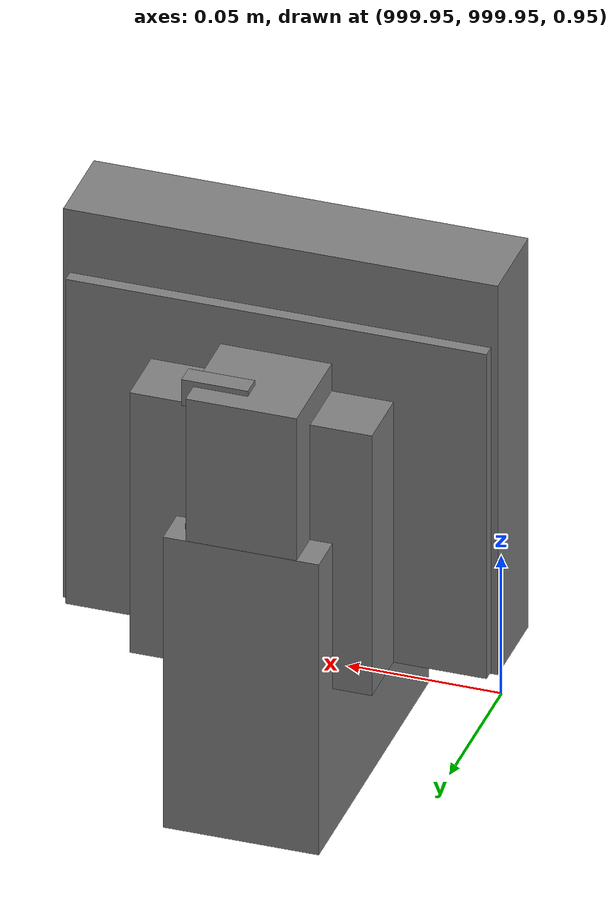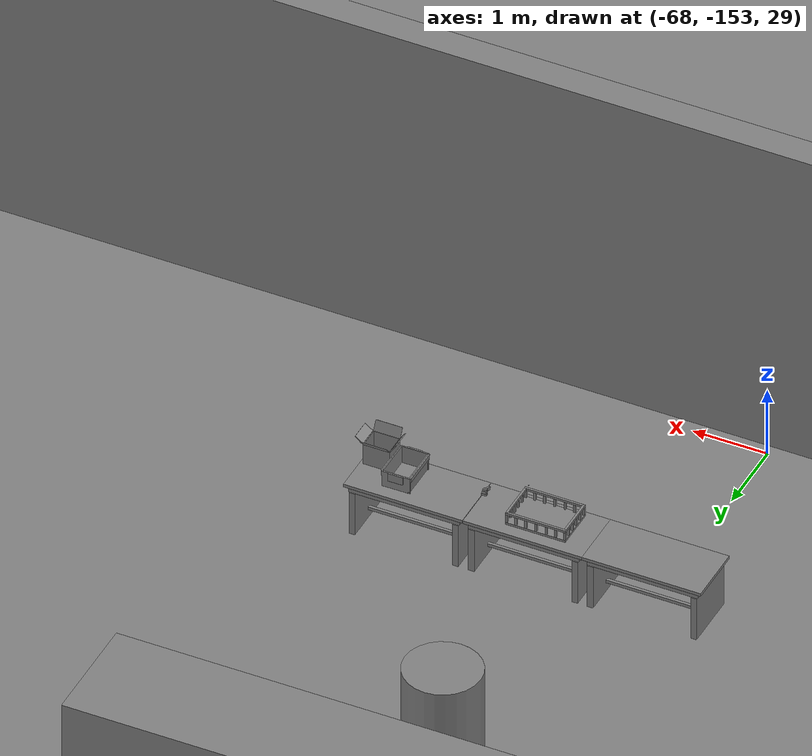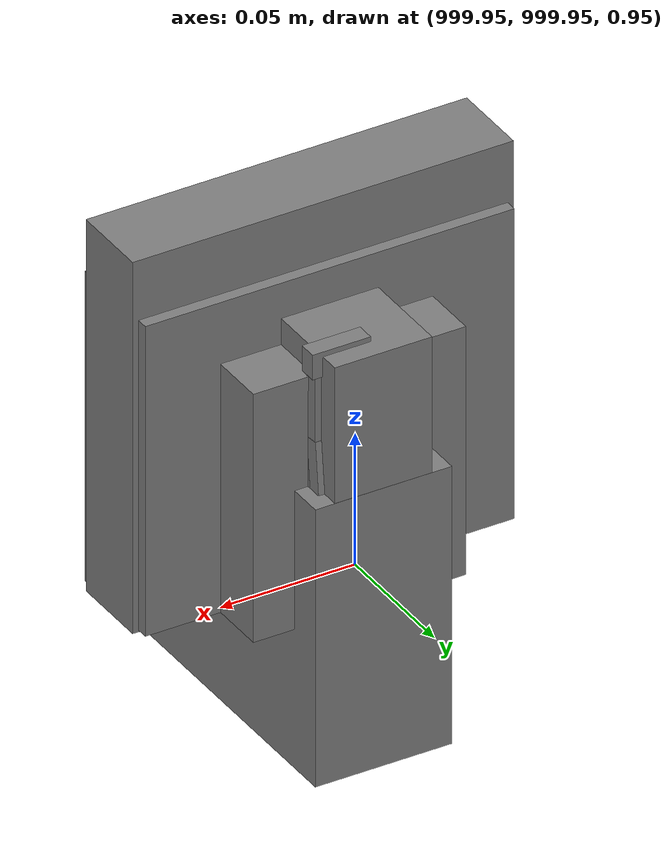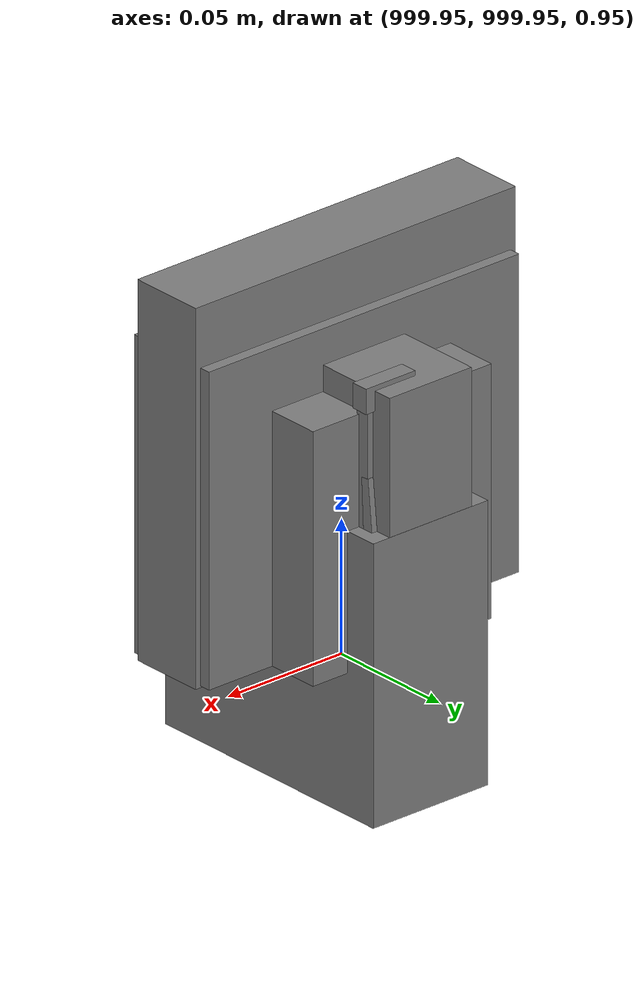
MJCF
<mujoco>
    <option gravity="0.000000000 0.000000000 -9.810000420" timestep="0.0049999999" integrator="implicitfast" density="1.225" viscosity="1.8000001e-05" noslip_iterations="10" iterations="100" sdf_iterations="50">
        <flag multiccd="disable"/>
    </option>
    <size memory="1000M"/>
    <compiler coordinate="local"/>
    <worldbody>
        <light cutoff="30" pos="0 1 1" dir="0 -1 -2"/>
        <light cutoff="30" pos="0 -1 1" dir="0 1 -2"/>
        <body pos="-66.225151062 -149.162582397 31.171817780" euler="-168.629745483 -15.015365601 2.962529898" mocap="true" name="spotlight1_SpotLight"/>
        <body pos="1000.000000000 999.999938965 1.000000000" euler="0.000000000 0.000000000 180.000000000" name="openloong_gripper_2f85_fix_base_usda_intelcore_i5">
            <geom contype="1" conaffinity="1" density="1000" type="box" material="" rgba="0.500000000 0.500000000 0.500000000 1.000000000" solimp="0.899999976 0.949999988 0.001000000" friction="1.000000000 0.005000000 0.000100000" solref="0.020000000 1.000000000" margin="0" condim="3" group="0" pos="0.000000000 0.000000000 0.051722717" quat="0.707106709 0.000000000 0.000000000 -0.707106769" size="0.052800000 0.018080002 0.052800000" name="openloong_gripper_2f85_fix_base_usda_geom_0903D344_3883_4F00_BD60_651B5E7BCDFF"/>
            <freejoint name="openloong_gripper_2f85_fix_base_usda_intelcore_i5_joint"/>
            <site size="0.005000000 0.005000000 0.005000000" rgba="0.500000000 0.500000000 0.500000000 1.000000000" pos="0.000000000 0.000000000 0.000000000" quat="0.999961913 0.008726534 0.000000000 0.000000000" group="0" type="sphere" name="openloong_gripper_2f85_fix_base_usda_intelcore_i5site"/>
        </body>
        <body pos="-65.992019653 -148.820693970 31.163341522" euler="-162.689285278 47.522495270 -23.964849472" mocap="true" name="spotlight2_SpotLight"/>
        <body pos="1000.000000000 1000.000000000 1.000000000" euler="0.000000000 0.000000000 180.000000000" name="openloong_gripper_2f85_fix_base_usda_wifi_box">
            <geom contype="1" conaffinity="1" density="1000" type="box" material="" rgba="0.500000000 0.500000000 0.500000000 1.000000000" solimp="0.899999976 0.949999988 0.001000000" friction="1.000000000 0.005000000 0.000100000" solref="0.020000000 1.000000000" margin="0" condim="3" group="0" pos="0.000000000 0.000000000 0.058978677" quat="0.000000000 0.000000047 0.000000000 1.000000000" size="0.068499997 0.018999999 0.059000000" name="openloong_gripper_2f85_fix_base_usda_geom_C670CFCE_4A51_45FE_8145_2C643567DA30"/>
            <freejoint name="openloong_gripper_2f85_fix_base_usda_wifi_box_joint"/>
            <site size="0.005000000 0.005000000 0.005000000" rgba="0.500000000 0.500000000 0.500000000 1.000000000" pos="0.000000000 0.000000000 0.000000000" quat="0.999961913 0.008726500 0.000000000 0.000000000" group="0" type="sphere" name="openloong_gripper_2f85_fix_base_usda_wifi_boxsite"/>
        </body>
        <body pos="1000.000000000 1000.000000000 1.000000000" euler="0.000011953 0.000005123 -179.999984741" name="openloong_gripper_2f85_fix_base_usda_intel_box">
            <geom contype="1" conaffinity="1" density="1000" type="box" material="" rgba="0.500000000 0.500000000 0.500000000 1.000000000" solimp="0.899999976 0.949999988 0.001000000" friction="1.000000000 0.005000000 0.000100000" solref="0.020000000 1.000000000" margin="0" condim="3" group="0" pos="0.000000000 -0.000067139 0.000082284" quat="0.707106709 0.000000225 0.000000253 0.707106650" size="0.052800003 0.025300000 0.052800003" name="openloong_gripper_2f85_fix_base_usda_geom_5F2A6224_1939_4EB6_8184_8BE53C47D071"/>
            <freejoint name="openloong_gripper_2f85_fix_base_usda_intel_box_joint"/>
            <site size="0.005000000 0.005000000 0.005000000" rgba="0.500000000 0.500000000 0.500000000 1.000000000" pos="0.000000000 0.000000000 0.000000000" quat="0.999961913 0.008726500 0.000000000 0.000000000" group="0" type="sphere" name="openloong_gripper_2f85_fix_base_usda_intel_boxsite"/>
        </body>
        <body pos="1000.000000000 1000.000000000 1.000000000" euler="0.000000000 0.000000000 180.000000000" name="openloong_gripper_2f85_fix_base_usda_cpu_fan">
            <geom contype="1" conaffinity="1" density="1000" type="box" material="" rgba="0.500000000 0.500000000 0.500000000 1.000000000" solimp="0.899999976 0.949999988 0.001000000" friction="1.000000000 0.005000000 0.000100000" solref="0.020000000 1.000000000" margin="0" condim="3" group="0" pos="0.000000000 0.000000000 0.070034981" quat="0.000000000 0.000000000 0.000000000 1.000000000" size="0.070700005 0.014699999 0.070700005" name="openloong_gripper_2f85_fix_base_usda_geom_B1E1D223_FB67_4D71_83A6_33CA4D439396"/>
            <freejoint name="openloong_gripper_2f85_fix_base_usda_cpu_fan_joint"/>
            <site size="0.005000000 0.005000000 0.005000000" rgba="0.500000000 0.500000000 0.500000000 1.000000000" pos="0.000000000 0.000000000 0.000000000" quat="0.999961913 0.008726535 0.000000000 0.000000000" group="0" type="sphere" name="openloong_gripper_2f85_fix_base_usda_cpu_fancsite"/>
        </body>
        <body pos="-66.092689514 -149.581481934 31.163526535" euler="135.952224731 76.863365173 -84.053771973" mocap="true" name="spotlight3_SpotLight"/>
        <body pos="1000.000000000 1000.000000000 1.000000000" euler="0.000000000 0.000000000 180.000000000" name="openloong_gripper_2f85_fix_base_usda_battery_01">
            <geom contype="1" conaffinity="1" density="1000" type="box" material="" rgba="0.500000000 0.500000000 0.500000000 1.000000000" solimp="0.899999976 0.949999988 0.001000000" friction="1.000000000 0.005000000 0.000100000" solref="0.020000000 1.000000000" margin="0" condim="3" group="0" pos="-0.011123657 -0.041940309 0.101691343" quat="1.000000000 0.000000000 0.000000000 0.000000000" size="0.010800000 0.003375000 0.004725000" name="openloong_gripper_2f85_fix_base_usda_geom_65E629B4_19C7_401F_969E_A2D924FFE1B0"/>
            <geom contype="1" conaffinity="1" density="1000" type="box" material="" rgba="0.500000000 0.500000000 0.500000000 1.000000000" solimp="0.899999976 0.949999988 0.001000000" friction="1.000000000 0.005000000 0.000100000" solref="0.020000000 1.000000000" margin="0" condim="3" group="0" pos="-0.010876465 -0.044247437 0.047066893" quat="0.998702705 -0.050920475 0.000000000 0.000000000" size="0.009450001 0.002700000 0.024975000" name="openloong_gripper_2f85_fix_base_usda_geom_BD7ECF35_6DB2_4BB0_94B0_A277BC7ADE2B"/>
            <geom contype="1" conaffinity="1" density="1000" type="box" material="" rgba="0.500000000 0.500000000 0.500000000 1.000000000" solimp="0.899999976 0.949999988 0.001000000" friction="1.000000000 0.005000000 0.000100000" solref="0.020000000 1.000000000" margin="0" condim="3" group="0" pos="-0.001235962 -0.000659180 0.047381196" quat="1.000000000 0.000000000 0.000000000 0.000000000" size="0.039420001 0.039150000 0.047250003" name="openloong_gripper_2f85_fix_base_usda_geom_F5060767_0D1B_4D84_BFD7_9B79F8437E3B"/>
            <geom contype="1" conaffinity="1" density="1000" type="box" material="" rgba="0.500000000 0.500000000 0.500000000 1.000000000" solimp="0.899999976 0.949999988 0.001000000" friction="1.000000000 0.005000000 0.000100000" solref="0.020000000 1.000000000" margin="0" condim="3" group="0" pos="-0.010876465 -0.039138794 0.009851727" quat="1.000000000 0.000000000 0.000000000 0.000000000" size="0.009450001 0.010800000 0.013500000" name="openloong_gripper_2f85_fix_base_usda_geom_52D682C8_0312_4411_AD8F_94256D776620"/>
            <geom contype="1" conaffinity="1" density="1000" type="box" material="" rgba="0.500000000 0.500000000 0.500000000 1.000000000" solimp="0.899999976 0.949999988 0.001000000" friction="1.000000000 0.005000000 0.000100000" solref="0.020000000 1.000000000" margin="0" condim="3" group="0" pos="-0.010876465 -0.041528322 0.071508206" quat="1.000000000 0.000000000 0.000000000 0.000000000" size="0.009450001 0.002700000 0.027000001" name="openloong_gripper_2f85_fix_base_usda_geom_5419449E_5DE1_4E0C_9F21_2BE2427E56B6"/>
            <freejoint name="openloong_gripper_2f85_fix_base_usda_battery_01_joint"/>
            <site size="0.005000000 0.005000000 0.005000000" rgba="0.500000000 0.500000000 0.500000000 1.000000000" pos="0.000000000 0.000000000 0.000000000" quat="0.999961913 0.008726500 0.000000000 0.000000000" group="0" type="sphere" name="openloong_gripper_2f85_fix_base_usda_battery_01site"/>
        </body>
        <body pos="-64.866622925 -149.383972168 30.183746338" euler="89.999984741 89.999946594 0.000000000" name="openloong_gripper_2f85_fix_base_usda_bluebox_01">
            <geom contype="1" conaffinity="1" density="1000" type="box" material="" rgba="0.500000000 0.500000000 0.500000000 1.000000000" solimp="0.899999976 0.949999988 0.001000000" friction="1.000000000 0.005000000 0.000100000" solref="0.020000000 1.000000000" margin="0" condim="3" group="0" pos="0.276580811 0.187225342 0.000068665" quat="0.707106948 0.000077471 0.707106352 0.000077486" size="0.100000001 0.057999998 0.010000000" name="openloong_gripper_2f85_fix_base_usda_geom_835CD103_109F_49C7_9D52_D3E773161D0D"/>
            <geom contype="1" conaffinity="1" density="1000" type="box" material="" rgba="0.500000000 0.500000000 0.500000000 1.000000000" solimp="0.899999976 0.949999988 0.001000000" friction="1.000000000 0.005000000 0.000100000" solref="0.020000000 1.000000000" margin="0" condim="3" group="0" pos="0.000000000 0.002883911 0.000000000" quat="0.999999881 0.000000000 0.000000000 0.000000000" size="0.254000008 0.003000000 0.172000006" name="openloong_gripper_2f85_fix_base_usda_geom_99AC102D_F789_4933_9FFD_9BA49180075C"/>
            <geom contype="1" conaffinity="1" density="1000" type="box" material="" rgba="0.500000000 0.500000000 0.500000000 1.000000000" solimp="0.899999976 0.949999988 0.001000000" friction="1.000000000 0.005000000 0.000100000" solref="0.020000000 1.000000000" margin="0" condim="3" group="0" pos="0.000000000 0.124874115 0.173484802" quat="0.999796331 0.020176515 -0.000000015 0.000000030" size="0.259999990 0.119999997 0.007000000" name="openloong_gripper_2f85_fix_base_usda_geom_C0D25494_75BC_488D_B31E_01B0AC6959FB"/>
            <geom contype="1" conaffinity="1" density="1000" type="box" material="" rgba="0.500000000 0.500000000 0.500000000 1.000000000" solimp="0.899999976 0.949999988 0.001000000" friction="1.000000000 0.005000000 0.000100000" solref="0.020000000 1.000000000" margin="0" condim="3" group="0" pos="0.000000000 0.124874115 -0.173469543" quat="0.999796331 -0.020176545 -0.000000015 0.000000000" size="0.259999990 0.119999997 0.007000000" name="openloong_gripper_2f85_fix_base_usda_geom_0590EA52_D662_48AA_A173_1C682AFD5B16"/>
            <geom contype="1" conaffinity="1" density="1000" type="box" material="" rgba="0.500000000 0.500000000 0.500000000 1.000000000" solimp="0.899999976 0.949999988 0.001000000" friction="1.000000000 0.005000000 0.000100000" solref="0.020000000 1.000000000" margin="0" condim="3" group="0" pos="0.000000000 0.214008331 0.188980103" quat="0.999912977 0.013176724 0.000000015 0.000000000" size="0.259999990 0.029999999 0.012500000" name="openloong_gripper_2f85_fix_base_usda_geom_F39F1060_7EE0_454D_9ADA_F7ADBD7DA77B"/>
            <geom contype="1" conaffinity="1" density="1000" type="box" material="" rgba="0.500000000 0.500000000 0.500000000 1.000000000" solimp="0.899999976 0.949999988 0.001000000" friction="1.000000000 0.005000000 0.000100000" solref="0.020000000 1.000000000" margin="0" condim="3" group="0" pos="-0.258361816 0.125289917 0.001876831" quat="0.702796936 -0.020792112 0.710783124 0.020769298" size="0.189999998 0.119999997 0.009000000" name="openloong_gripper_2f85_fix_base_usda_geom_36BAC8EF_DC66_40EE_BCCD_7C75BCB5E7AF"/>
            <geom contype="1" conaffinity="1" density="1000" type="box" material="" rgba="0.500000000 0.500000000 0.500000000 1.000000000" solimp="0.899999976 0.949999988 0.001000000" friction="1.000000000 0.005000000 0.000100000" solref="0.020000000 1.000000000" margin="0" condim="3" group="0" pos="0.000000000 0.214008331 -0.188980103" quat="0.999912977 -0.013176769 0.000000030 0.000000015" size="0.259999990 0.029999999 0.012500000" name="openloong_gripper_2f85_fix_base_usda_geom_EDF18D2D_6096_4365_BC5B_0585B9DE72C9"/>
            <geom contype="1" conaffinity="1" density="1000" type="box" material="" rgba="0.500000000 0.500000000 0.500000000 1.000000000" solimp="0.899999976 0.949999988 0.001000000" friction="1.000000000 0.005000000 0.000100000" solref="0.020000000 1.000000000" margin="0" condim="3" group="0" pos="-0.276611328 0.187225342 0.000068665" quat="0.707106650 0.000077441 0.707106709 0.000077456" size="0.100000001 0.057999998 0.010000000" name="openloong_gripper_2f85_fix_base_usda_geom_84FDF16A_B16E_4DCB_8A3B_91B52FDBF84D"/>
            <geom contype="1" conaffinity="1" density="1000" type="box" material="" rgba="0.500000000 0.500000000 0.500000000 1.000000000" solimp="0.899999976 0.949999988 0.001000000" friction="1.000000000 0.005000000 0.000100000" solref="0.020000000 1.000000000" margin="0" condim="3" group="0" pos="0.258331299 0.125289917 0.001876831" quat="0.702851415 0.018856421 0.710823774 -0.019329369" size="0.189999998 0.119999997 0.009000000" name="openloong_gripper_2f85_fix_base_usda_geom_F5916FEB_F004_4C98_87A4_0B755CC4155A"/>
            <freejoint name="openloong_gripper_2f85_fix_base_usda_bluebox_01_joint"/>
            <site size="0.005000000 0.005000000 0.005000000" rgba="0.500000000 0.500000000 0.500000000 1.000000000" pos="0.000000000 0.000000000 0.000000000" quat="0.999961913 0.008726534 0.000000000 0.000000000" group="0" type="sphere" name="openloong_gripper_2f85_fix_base_usda_bluebox_01site"/>
        </body>
        <body pos="-64.496299744 -149.491867065 30.235729218" euler="0.000000000 0.000000000 89.999946594" name="openloong_gripper_2f85_fix_base_usda_cardboardbox_01">
            <geom contype="1" conaffinity="1" density="1000" type="box" material="" rgba="0.500000000 0.500000000 0.500000000 1.000000000" solimp="0.899999976 0.949999988 0.001000000" friction="1.000000000 0.005000000 0.000100000" solref="0.020000000 1.000000000" margin="0" condim="3" group="0" pos="-0.003166199 -0.004086494 0.005052090" quat="1.000000000 0.000000000 0.000000000 0.000000000" size="0.142499998 0.177500010 0.005000000" name="openloong_gripper_2f85_fix_base_usda_geom_060A7DD1_04A4_41B8_ADD2_BFF42D8A14CE"/>
            <geom contype="1" conaffinity="1" density="1000" type="box" material="" rgba="0.500000000 0.500000000 0.500000000 1.000000000" solimp="0.899999976 0.949999988 0.001000000" friction="1.000000000 0.005000000 0.000100000" solref="0.020000000 1.000000000" margin="0" condim="3" group="0" pos="-0.003166199 0.170316696 0.150570869" quat="1.000000000 0.000000000 0.000000000 0.000000000" size="0.142499998 0.005000000 0.149999991" name="openloong_gripper_2f85_fix_base_usda_geom_95FF0C0C_3E43_4A7D_B6E6_C4CD19070D9C"/>
            <geom contype="1" conaffinity="1" density="1000" type="box" material="" rgba="0.500000000 0.500000000 0.500000000 1.000000000" solimp="0.899999976 0.949999988 0.001000000" friction="1.000000000 0.005000000 0.000100000" solref="0.020000000 1.000000000" margin="0" condim="3" group="0" pos="-0.147399902 -0.005307198 0.150570869" quat="1.000000000 0.000000000 0.000000000 0.000000000" size="0.005000000 0.177500010 0.149999991" name="openloong_gripper_2f85_fix_base_usda_geom_0DB02151_096E_4E1E_BFB1_B521B2E724DA"/>
            <geom contype="1" conaffinity="1" density="1000" type="box" material="" rgba="0.500000000 0.500000000 0.500000000 1.000000000" solimp="0.899999976 0.949999988 0.001000000" friction="1.000000000 0.005000000 0.000100000" solref="0.020000000 1.000000000" margin="0" condim="3" group="0" pos="0.140275955 -0.005307198 0.150570869" quat="1.000000000 0.000000000 0.000000000 0.000000000" size="0.005000000 0.177500010 0.149999991" name="openloong_gripper_2f85_fix_base_usda_geom_9DBD81CB_AA74_418D_A2C5_5DB9F5B5D306"/>
            <geom contype="1" conaffinity="1" density="1000" type="box" material="" rgba="0.500000000 0.500000000 0.500000000 1.000000000" solimp="0.899999976 0.949999988 0.001000000" friction="1.000000000 0.005000000 0.000100000" solref="0.020000000 1.000000000" margin="0" condim="3" group="0" pos="-0.003166199 -0.181550980 0.150570869" quat="1.000000000 0.000000000 0.000000000 0.000000000" size="0.142499998 0.005000000 0.149999991" name="openloong_gripper_2f85_fix_base_usda_geom_7773A90E_C882_4DD0_B1A0_D6888B2B0FC1"/>
            <freejoint name="openloong_gripper_2f85_fix_base_usda_cardboardbox_01_joint"/>
            <site size="0.005000000 0.005000000 0.005000000" rgba="0.500000000 0.500000000 0.500000000 1.000000000" pos="0.000000000 0.000000000 0.000000000" quat="0.999961913 0.008726535 0.000000000 0.000000000" group="0" type="sphere" name="openloong_gripper_2f85_fix_base_usda_site_B72F419F_B6D7_4E07_8FAB_1C506B5EE7A9"/>
            <body pos="0.139160156 -0.004048347 0.301930904" euler="-179.999954224 49.383502960 179.999954224" name="openloong_gripper_2f85_fix_base_usda_A1_006">
                <geom contype="1" conaffinity="1" density="1000" type="box" material="" rgba="0.500000000 0.500000000 0.500000000 1.000000000" solimp="0.899999976 0.949999988 0.001000000" friction="1.000000000 0.005000000 0.000100000" solref="0.020000000 1.000000000" margin="0" condim="3" group="0" pos="-0.071587563 0.000009537 0.001745224" quat="0.999999881 0.000000000 0.000000000 0.000000000" size="0.071249999 0.179999992 0.002500000" name="openloong_gripper_2f85_fix_base_usda_geom_3856CBCC_A633_40B7_8C99_F800CEF856F0"/>
                <joint armature="0" stiffness="0.07" damping="0.0099999998" axis="0.000000 1.000000 0.000000" type="hinge" name="openloong_gripper_2f85_fix_base_usda_A1_006"/>
            </body>
            <body pos="-0.145902634 -0.004086494 0.301938057" euler="-180.000000000 -60.000011444 -180.000000000" name="openloong_gripper_2f85_fix_base_usda_A2_006">
                <geom contype="1" conaffinity="1" density="1000" type="box" material="" rgba="0.500000000 0.500000000 0.500000000 1.000000000" solimp="0.899999976 0.949999988 0.001000000" friction="1.000000000 0.005000000 0.000100000" solref="0.020000000 1.000000000" margin="0" condim="3" group="0" pos="0.071268082 0.000009537 0.002717972" quat="0.000002921 0.000000000 -0.000000030 0.999999881" size="0.071249999 0.179999992 0.002500000" name="openloong_gripper_2f85_fix_base_usda_geom_C467FD0B_3F45_4852_B52C_DF00F9D1075C"/>
                <joint armature="0" stiffness="0.07" damping="0.0099999998" axis="0.000000 1.000000 0.000000" type="hinge" name="openloong_gripper_2f85_fix_base_usda_A2_006"/>
            </body>
            <body pos="-0.003385544 0.175991058 0.301930904" euler="-125.858116150 -0.000004561 0.000002331" name="openloong_gripper_2f85_fix_base_usda_B2_006">
                <geom contype="1" conaffinity="1" density="1000" type="box" material="" rgba="0.500000000 0.500000000 0.500000000 1.000000000" solimp="0.899999976 0.949999988 0.001000000" friction="1.000000000 0.005000000 0.000100000" solref="0.020000000 1.000000000" margin="0" condim="3" group="0" pos="0.000009537 -0.070939064 -0.002470016" quat="0.999614120 0.027776197 -0.000000015 0.000000030" size="0.137500003 0.064999998 0.005000000" name="openloong_gripper_2f85_fix_base_usda_geom_7CEAB4F9_8E43_468B_8259_D0E9541D7AB1"/>
                <joint armature="0" stiffness="0.07" damping="0.0099999998" axis="1.000000 0.000000 0.000000" type="hinge" name="openloong_gripper_2f85_fix_base_usda_B2_006"/>
            </body>
            <body pos="-0.003385544 -0.184140205 0.301938057" euler="147.805557251 0.000000000 0.000000000" name="openloong_gripper_2f85_fix_base_usda_B1_006">
                <geom contype="1" conaffinity="1" density="1000" type="box" material="" rgba="0.500000000 0.500000000 0.500000000 1.000000000" solimp="0.899999976 0.949999988 0.001000000" friction="1.000000000 0.005000000 0.000100000" solref="0.020000000 1.000000000" margin="0" condim="3" group="0" pos="-0.000028610 0.070202351 -0.002703667" quat="0.999614179 -0.027776167 0.000000000 0.000000000" size="0.137500003 0.064999998 0.005000000" name="openloong_gripper_2f85_fix_base_usda_geom_E15143F6_9C8E_4E2D_BC84_AC2DD799BDB4"/>
                <joint armature="0" stiffness="0.07" damping="0.0099999998" axis="1.000000 0.000000 0.000000" type="hinge" name="openloong_gripper_2f85_fix_base_usda_B1_006"/>
            </body>
        </body>
        <body pos="-65.882858276 -149.481979370 30.229999542" euler="-64.487716675 0.000000000 0.000000000" name="openloong_gripper_2f85_fix_base_usda_Barcode">
            <geom contype="1" conaffinity="1" density="1000" type="box" material="" rgba="0.500000000 0.500000000 0.500000000 1.000000000" solimp="0.899999976 0.949999988 0.001000000" friction="1.000000000 0.005000000 0.000100000" solref="0.020000000 1.000000000" margin="0" condim="3" group="0" pos="0.000000000 0.013038635 0.001419067" quat="0.000000000 0.000000000 0.000000000 1.000000119" size="0.034000002 0.010000000 0.017999999" name="openloong_gripper_2f85_fix_base_usda_geom_301E4822_EAFC_473A_B7DE_2F1F6BBB7957"/>
            <geom contype="1" conaffinity="1" density="1000" type="box" material="" rgba="0.500000000 0.500000000 0.500000000 1.000000000" solimp="0.899999976 0.949999988 0.001000000" friction="1.000000000 0.005000000 0.000100000" solref="0.020000000 1.000000000" margin="0" condim="3" group="0" pos="0.000000000 -0.035301208 -0.007095337" quat="0.000000000 0.000000000 -0.043619365 0.999048233" size="0.028999999 0.010000000 0.020000000" name="openloong_gripper_2f85_fix_base_usda_geom_51CF8DFD_8D56_4025_9374_D0840643362D"/>
            <geom contype="1" conaffinity="1" density="1000" type="box" material="" rgba="0.500000000 0.500000000 0.500000000 1.000000000" solimp="0.899999976 0.949999988 0.001000000" friction="1.000000000 0.005000000 0.000100000" solref="0.020000000 1.000000000" margin="0" condim="3" group="0" pos="0.000000000 -0.043411255 -0.011749268" quat="0.922262907 0.386563420 0.000000000 0.000000000" size="0.026000001 0.010000000 0.020000000" name="openloong_gripper_2f85_fix_base_usda_geom_A6DE6E81_510A_4A33_842E_2AC819C09FDE"/>
            <geom contype="1" conaffinity="1" density="1000" type="box" material="" rgba="0.500000000 0.500000000 0.500000000 1.000000000" solimp="0.899999976 0.949999988 0.001000000" friction="1.000000000 0.005000000 0.000100000" solref="0.020000000 1.000000000" margin="0" condim="3" group="0" pos="0.000000000 -0.016967773 -0.031860352" quat="0.000000000 0.000000000 0.000000000 1.000000119" size="0.008000000 0.010000000 0.013000000" name="openloong_gripper_2f85_fix_base_usda_geom_28BDD3BA_0363_46C8_B97C_52A57A4D9725"/>
            <geom contype="1" conaffinity="1" density="1000" type="box" material="" rgba="0.500000000 0.500000000 0.500000000 1.000000000" solimp="0.899999976 0.949999988 0.001000000" friction="1.000000000 0.005000000 0.000100000" solref="0.020000000 1.000000000" margin="0" condim="3" group="0" pos="0.000000000 -0.001869202 0.000312805" quat="0.953716993 0.300705761 0.000000000 0.000000000" size="0.032000002 0.010000000 0.018999999" name="openloong_gripper_2f85_fix_base_usda_geom_C6AF4225_33D4_4F8F_9778_B78A91249ED2"/>
            <geom contype="1" conaffinity="1" density="1000" type="box" material="" rgba="0.500000000 0.500000000 0.500000000 1.000000000" solimp="0.899999976 0.949999988 0.001000000" friction="1.000000000 0.005000000 0.000100000" solref="0.020000000 1.000000000" margin="0" condim="3" group="0" pos="0.000000000 -0.019531250 -0.003173828" quat="0.953716993 0.300705761 0.000000000 0.000000000" size="0.030999999 0.010000000 0.020000000" name="openloong_gripper_2f85_fix_base_usda_geom_CE713627_9CC8_40F4_8C80_C8A7DE52200D"/>
            <geom contype="1" conaffinity="1" density="1000" type="box" material="" rgba="0.500000000 0.500000000 0.500000000 1.000000000" solimp="0.899999976 0.949999988 0.001000000" friction="1.000000000 0.005000000 0.000100000" solref="0.020000000 1.000000000" margin="0" condim="3" group="0" pos="0.000000000 -0.035301208 -0.007095337" quat="0.953716993 0.300705761 0.000000000 0.000000000" size="0.028999999 0.010000000 0.020000000" name="openloong_gripper_2f85_fix_base_usda_geom_E240B392_C113_4AA2_94A9_D28D820BE1CF"/>
            <geom contype="1" conaffinity="1" density="1000" type="box" material="" rgba="0.500000000 0.500000000 0.500000000 1.000000000" solimp="0.899999976 0.949999988 0.001000000" friction="1.000000000 0.005000000 0.000100000" solref="0.020000000 1.000000000" margin="0" condim="3" group="0" pos="0.000000000 -0.042617798 -0.071121216" quat="0.000000000 0.000000000 0.000000000 1.000000119" size="0.013000000 0.021000000 0.059999999" name="openloong_gripper_2f85_fix_base_usda_geom_3DD9B695_9755_4BB0_AE18_EB2CD01EDB00"/>
            <freejoint name="openloong_gripper_2f85_fix_base_usda_Barcode_joint"/>
            <site size="0.005000000 0.005000000 0.005000000" rgba="0.500000000 0.500000000 0.500000000 1.000000000" pos="0.000000000 0.000000000 0.000000000" quat="1.000000000 0.000000000 0.000000000 0.000000000" group="0" type="sphere" name="openloong_gripper_2f85_fix_base_usda_Barcode_site"/>
        </body>
        <body pos="-66.745018005 -149.392349243 30.184000015" euler="0.000000000 0.000000000 89.999946594" name="[22333379726335]_Basket_01">
            <geom contype="1" conaffinity="1" density="1000" type="box" material="" rgba="0.500000000 0.500000000 0.500000000 1.000000000" solimp="0.899999976 0.949999988 0.001000000" friction="1.000000000 0.005000000 0.000100000" solref="0.020000000 1.000000000" margin="0" condim="3" group="0" pos="-0.052425385 0.389207840 0.089787483" quat="0.707107008 0.000000000 0.000000000 0.707106411" size="0.014249999 0.014249999 0.059999999" name="[22333379726335]_geom_50E82384_237E_4501_83BF_21F01B016825"/>
            <geom contype="1" conaffinity="1" density="1000" type="box" material="" rgba="0.500000000 0.500000000 0.500000000 1.000000000" solimp="0.899999976 0.949999988 0.001000000" friction="1.000000000 0.005000000 0.000100000" solref="0.020000000 1.000000000" margin="0" condim="3" group="0" pos="0.264015198 -0.133043289 0.089787483" quat="0.707107008 0.000000000 0.000000000 0.707106411" size="0.014249999 0.014249999 0.059999999" name="[22333379726335]_geom_FC2C9A71_AFA1_4458_A577_F2D05D9FBCFE"/>
            <geom contype="1" conaffinity="1" density="1000" type="box" material="" rgba="0.500000000 0.500000000 0.500000000 1.000000000" solimp="0.899999976 0.949999988 0.001000000" friction="1.000000000 0.005000000 0.000100000" solref="0.020000000 1.000000000" margin="0" condim="3" group="0" pos="-0.264015198 -0.265548706 0.089793205" quat="0.707107008 0.000000000 0.000000000 0.707106411" size="0.014249999 0.014249999 0.059999999" name="[22333379726335]_geom_A9437D99_1BC1_4254_BD31_3C0063D88D24"/>
            <geom contype="1" conaffinity="1" density="1000" type="box" material="" rgba="0.500000000 0.500000000 0.500000000 1.000000000" solimp="0.899999976 0.949999988 0.001000000" friction="1.000000000 0.005000000 0.000100000" solref="0.020000000 1.000000000" margin="0" condim="3" group="0" pos="-0.160263062 -0.389322281 0.089793205" quat="0.707107008 0.000000000 0.000000000 0.707106411" size="0.014249999 0.014249999 0.059999999" name="[22333379726335]_geom_382CFDD0_A15E_452D_A524_620FB80A93B6"/>
            <geom contype="1" conaffinity="1" density="1000" type="box" material="" rgba="0.500000000 0.500000000 0.500000000 1.000000000" solimp="0.899999976 0.949999988 0.001000000" friction="1.000000000 0.005000000 0.000100000" solref="0.020000000 1.000000000" margin="0" condim="3" group="0" pos="0.162265778 -0.389322281 0.089787483" quat="0.707107008 0.000000000 0.000000000 0.707106411" size="0.014249999 0.014249999 0.059999999" name="[22333379726335]_geom_CBB354B0_E8E0_4E8A_B067_B943E6D08118"/>
            <geom contype="1" conaffinity="1" density="1000" type="box" material="" rgba="0.500000000 0.500000000 0.500000000 1.000000000" solimp="0.899999976 0.949999988 0.001000000" friction="1.000000000 0.005000000 0.000100000" solref="0.020000000 1.000000000" margin="0" condim="3" group="0" pos="0.264015198 0.389207840 0.089787483" quat="0.707107008 0.000000000 0.000000000 0.707106411" size="0.014249999 0.014249999 0.059999999" name="[22333379726335]_geom_0E57C224_03EC_4A66_8492_6F2C88512606"/>
            <geom contype="1" conaffinity="1" density="1000" type="box" material="" rgba="0.500000000 0.500000000 0.500000000 1.000000000" solimp="0.899999976 0.949999988 0.001000000" friction="1.000000000 0.005000000 0.000100000" solref="0.020000000 1.000000000" margin="0" condim="3" group="0" pos="-0.264015198 -0.133043289 0.089793205" quat="0.707107008 0.000000000 0.000000000 0.707106411" size="0.014249999 0.014249999 0.059999999" name="[22333379726335]_geom_C7DC5EEC_D90D_43A3_80EB_446090D91EDF"/>
            <geom contype="1" conaffinity="1" density="1000" type="box" material="" rgba="0.500000000 0.500000000 0.500000000 1.000000000" solimp="0.899999976 0.949999988 0.001000000" friction="1.000000000 0.005000000 0.000100000" solref="0.020000000 1.000000000" margin="0" condim="3" group="0" pos="-0.264026642 0.269256592 0.089793205" quat="0.707107008 0.000000000 0.000000000 0.707106411" size="0.014249999 0.014249999 0.059999999" name="[22333379726335]_geom_8264573C_38F4_44ED_A4B1_668E46B2FFFD"/>
            <geom contype="1" conaffinity="1" density="1000" type="box" material="" rgba="0.500000000 0.500000000 0.500000000 1.000000000" solimp="0.899999976 0.949999988 0.001000000" friction="1.000000000 0.005000000 0.000100000" solref="0.020000000 1.000000000" margin="0" condim="3" group="0" pos="0.054462433 0.389207840 0.089787483" quat="0.707107008 0.000000000 0.000000000 0.707106411" size="0.014249999 0.014249999 0.059999999" name="[22333379726335]_geom_C7230A96_C14A_4247_8137_E86BD7D549C1"/>
            <geom contype="1" conaffinity="1" density="1000" type="box" material="" rgba="0.500000000 0.500000000 0.500000000 1.000000000" solimp="0.899999976 0.949999988 0.001000000" friction="1.000000000 0.005000000 0.000100000" solref="0.020000000 1.000000000" margin="0" condim="3" group="0" pos="0.054462433 -0.389322281 0.089787483" quat="0.707107008 0.000000000 0.000000000 0.707106411" size="0.014249999 0.014249999 0.059999999" name="[22333379726335]_geom_6F8D5F2A_0D03_4148_A815_8CCD481FB0C9"/>
            <geom contype="1" conaffinity="1" density="1000" type="box" material="" rgba="0.500000000 0.500000000 0.500000000 1.000000000" solimp="0.899999976 0.949999988 0.001000000" friction="1.000000000 0.005000000 0.000100000" solref="0.020000000 1.000000000" margin="0" condim="3" group="0" pos="0.264015198 0.269256592 0.089793205" quat="0.707107008 0.000000000 0.000000000 0.707106411" size="0.014249999 0.014249999 0.059999999" name="[22333379726335]_geom_371CD85E_4EE9_406F_92FE_E1B71D26B9E8"/>
            <geom contype="1" conaffinity="1" density="1000" type="box" material="" rgba="0.500000000 0.500000000 0.500000000 1.000000000" solimp="0.899999976 0.949999988 0.001000000" friction="1.000000000 0.005000000 0.000100000" solref="0.020000000 1.000000000" margin="0" condim="3" group="0" pos="0.264015198 -0.389322281 0.089787483" quat="0.707107008 0.000000000 0.000000000 0.707106411" size="0.014249999 0.014249999 0.059999999" name="[22333379726335]_geom_A182A6FC_4BC4_4499_B98B_F192EC47C9F1"/>
            <geom contype="1" conaffinity="1" density="1000" type="box" material="" rgba="0.500000000 0.500000000 0.500000000 1.000000000" solimp="0.899999976 0.949999988 0.001000000" friction="1.000000000 0.005000000 0.000100000" solref="0.020000000 1.000000000" margin="0" condim="3" group="0" pos="0.000000000 0.000000000 0.015998840" quat="0.707107008 0.000000000 0.000000000 0.707106411" size="0.403499991 0.279000014 0.015750000" name="[22333379726335]_geom_925404A2_5F4E_4868_8F3A_3E2C396671C6"/>
            <geom contype="1" conaffinity="1" density="1000" type="box" material="" rgba="0.500000000 0.500000000 0.500000000 1.000000000" solimp="0.899999976 0.949999988 0.001000000" friction="1.000000000 0.005000000 0.000100000" solref="0.020000000 1.000000000" margin="0" condim="3" group="0" pos="0.000000000 -0.389476776 0.163619041" quat="0.707107008 0.000000000 0.000000000 0.707106411" size="0.015000000 0.277500004 0.015750000" name="[22333379726335]_geom_BE784763_0D6C_4B11_B464_53975EB20E0B"/>
            <geom contype="1" conaffinity="1" density="1000" type="box" material="" rgba="0.500000000 0.500000000 0.500000000 1.000000000" solimp="0.899999976 0.949999988 0.001000000" friction="1.000000000 0.005000000 0.000100000" solref="0.020000000 1.000000000" margin="0" condim="3" group="0" pos="0.162265778 0.389207840 0.089787483" quat="0.707107008 0.000000000 0.000000000 0.707106411" size="0.014249999 0.014249999 0.059999999" name="[22333379726335]_geom_485F2AAE_97DB_48FB_8D47_CF41CFDABA2C"/>
            <geom contype="1" conaffinity="1" density="1000" type="box" material="" rgba="0.500000000 0.500000000 0.500000000 1.000000000" solimp="0.899999976 0.949999988 0.001000000" friction="1.000000000 0.005000000 0.000100000" solref="0.020000000 1.000000000" margin="0" condim="3" group="0" pos="0.000000000 0.389471054 0.163619041" quat="0.707107008 0.000000000 0.000000000 0.707106411" size="0.015000000 0.277500004 0.015750000" name="[22333379726335]_geom_9DCA91B8_AA2B_4487_ADEB_43136760D1A4"/>
            <geom contype="1" conaffinity="1" density="1000" type="box" material="" rgba="0.500000000 0.500000000 0.500000000 1.000000000" solimp="0.899999976 0.949999988 0.001000000" friction="1.000000000 0.005000000 0.000100000" solref="0.020000000 1.000000000" margin="0" condim="3" group="0" pos="-0.263511658 0.000000000 0.163619041" quat="0.707107008 0.000000000 0.000000000 0.707106411" size="0.403499991 0.015000000 0.015750000" name="[22333379726335]_geom_A296BF6A_EB02_4A8F_990B_A2A22FC2EBEF"/>
            <geom contype="1" conaffinity="1" density="1000" type="box" material="" rgba="0.500000000 0.500000000 0.500000000 1.000000000" solimp="0.899999976 0.949999988 0.001000000" friction="1.000000000 0.005000000 0.000100000" solref="0.020000000 1.000000000" margin="0" condim="3" group="0" pos="-0.264015198 0.141334534 0.089793205" quat="0.707107008 0.000000000 0.000000000 0.707106411" size="0.014249999 0.014249999 0.059999999" name="[22333379726335]_geom_6551575F_A4F9_449C_8F3B_9C1CEEFA6C0F"/>
            <geom contype="1" conaffinity="1" density="1000" type="box" material="" rgba="0.500000000 0.500000000 0.500000000 1.000000000" solimp="0.899999976 0.949999988 0.001000000" friction="1.000000000 0.005000000 0.000100000" solref="0.020000000 1.000000000" margin="0" condim="3" group="0" pos="0.264015198 -0.265548706 0.089787483" quat="0.707107008 0.000000000 0.000000000 0.707106411" size="0.014249999 0.014249999 0.059999999" name="[22333379726335]_geom_82A9AB14_1AC4_42DD_BE76_AF66BD6C5384"/>
            <geom contype="1" conaffinity="1" density="1000" type="box" material="" rgba="0.500000000 0.500000000 0.500000000 1.000000000" solimp="0.899999976 0.949999988 0.001000000" friction="1.000000000 0.005000000 0.000100000" solref="0.020000000 1.000000000" margin="0" condim="3" group="0" pos="-0.160263062 0.389207840 0.089787483" quat="0.707107008 0.000000000 0.000000000 0.707106411" size="0.014249999 0.014249999 0.059999999" name="[22333379726335]_geom_87B3BC4A_667F_4607_ADDB_77B68D2AD1CF"/>
            <geom contype="1" conaffinity="1" density="1000" type="box" material="" rgba="0.500000000 0.500000000 0.500000000 1.000000000" solimp="0.899999976 0.949999988 0.001000000" friction="1.000000000 0.005000000 0.000100000" solref="0.020000000 1.000000000" margin="0" condim="3" group="0" pos="-0.052425385 -0.389322281 0.089787483" quat="0.707107008 0.000000000 0.000000000 0.707106411" size="0.014249999 0.014249999 0.059999999" name="[22333379726335]_geom_755B0443_3E7E_4D7D_BD9D_98BDBF2BAF3F"/>
            <geom contype="1" conaffinity="1" density="1000" type="box" material="" rgba="0.500000000 0.500000000 0.500000000 1.000000000" solimp="0.899999976 0.949999988 0.001000000" friction="1.000000000 0.005000000 0.000100000" solref="0.020000000 1.000000000" margin="0" condim="3" group="0" pos="-0.264026642 -0.389322281 0.089793205" quat="0.707107008 0.000000000 0.000000000 0.707106411" size="0.014249999 0.014249999 0.059999999" name="[22333379726335]_geom_92AA45E4_D33D_4C67_BB04_409D39AABFFD"/>
            <geom contype="1" conaffinity="1" density="1000" type="box" material="" rgba="0.500000000 0.500000000 0.500000000 1.000000000" solimp="0.899999976 0.949999988 0.001000000" friction="1.000000000 0.005000000 0.000100000" solref="0.020000000 1.000000000" margin="0" condim="3" group="0" pos="0.264015198 0.141334534 0.089787483" quat="0.707107008 0.000000000 0.000000000 0.707106411" size="0.014249999 0.014249999 0.059999999" name="[22333379726335]_geom_73C90F89_D836_4D79_80BB_115424BB99CE"/>
            <geom contype="1" conaffinity="1" density="1000" type="box" material="" rgba="0.500000000 0.500000000 0.500000000 1.000000000" solimp="0.899999976 0.949999988 0.001000000" friction="1.000000000 0.005000000 0.000100000" solref="0.020000000 1.000000000" margin="0" condim="3" group="0" pos="-0.264015198 0.389207840 0.089793205" quat="0.707107008 0.000000000 0.000000000 0.707106411" size="0.014249999 0.014249999 0.059999999" name="[22333379726335]_geom_C8E755BE_82FC_4C08_BFFA_98DC533D591D"/>
            <geom contype="1" conaffinity="1" density="1000" type="box" material="" rgba="0.500000000 0.500000000 0.500000000 1.000000000" solimp="0.899999976 0.949999988 0.001000000" friction="1.000000000 0.005000000 0.000100000" solref="0.020000000 1.000000000" margin="0" condim="3" group="0" pos="0.264015198 0.004480362 0.089787483" quat="0.707107008 0.000000000 0.000000000 0.707106411" size="0.014249999 0.014249999 0.059999999" name="[22333379726335]_geom_AA6E9DD6_18F5_45F8_94A6_5A4E3AC16564"/>
            <geom contype="1" conaffinity="1" density="1000" type="box" material="" rgba="0.500000000 0.500000000 0.500000000 1.000000000" solimp="0.899999976 0.949999988 0.001000000" friction="1.000000000 0.005000000 0.000100000" solref="0.020000000 1.000000000" margin="0" condim="3" group="0" pos="0.263694763 -0.000011444 0.163619041" quat="0.707107008 0.000000000 0.000000000 0.707106411" size="0.403499991 0.015000000 0.015750000" name="[22333379726335]_geom_39DEB423_BDD0_40A1_B25D_BF6BEC8111EE"/>
            <geom contype="1" conaffinity="1" density="1000" type="box" material="" rgba="0.500000000 0.500000000 0.500000000 1.000000000" solimp="0.899999976 0.949999988 0.001000000" friction="1.000000000 0.005000000 0.000100000" solref="0.020000000 1.000000000" margin="0" condim="3" group="0" pos="-0.264015198 0.004480362 0.089793205" quat="0.707107008 0.000000000 0.000000000 0.707106411" size="0.014249999 0.014249999 0.059999999" name="[22333379726335]_geom_DED63B2A_91AC_4619_8D24_C8027AC1D0B1"/>
            <freejoint name="[22333379726335]_joint_6158D7E8_FC12_4BD4_8F0F_704F6692DDAD"/>
        </body>
        <body pos="0.000000000 0.000000000 0.000000000" euler="0.000000000 0.000000000 0.000000000" name="Static Objects_Static Objects">
            <geom contype="1" conaffinity="1" density="1000" type="box" material="" rgba="0.500000000 0.500000000 0.500000000 1.000000000" solimp="0.899999976 0.949999988 0.001000000" friction="1.000000000 0.005000000 0.000100000" solref="0.020000000 1.000000000" margin="0" condim="3" group="0" pos="-67.544113159 -149.365814209 29.727830887" quat="0.500000417 0.499999970 0.499999553 0.499999970" size="0.381000012 0.319999993 0.041000001" name="Static Objects_geom_148F8D29_F737_4E01_B586_BAEE99E1BAC7"/>
            <geom contype="1" conaffinity="1" density="1000" type="box" material="" rgba="0.500000000 0.500000000 0.500000000 1.000000000" solimp="0.899999976 0.949999988 0.001000000" friction="1.000000000 0.005000000 0.000100000" solref="0.020000000 1.000000000" margin="0" condim="3" group="0" pos="-68.239501953 -149.365814209 30.086868286" quat="0.500000417 0.499999970 0.499999553 0.499999970" size="0.370999992 0.039500002 0.745000005" name="Static Objects_geom_02FE3322_AE29_4C94_8143_C874BDCF08B8"/>
            <geom contype="1" conaffinity="1" density="1000" type="box" material="" rgba="0.500000000 0.500000000 0.500000000 1.000000000" solimp="0.899999976 0.949999988 0.001000000" friction="1.000000000 0.005000000 0.000100000" solref="0.020000000 1.000000000" margin="0" condim="3" group="0" pos="-68.239501953 -149.365814209 30.147235870" quat="0.500000417 0.499999970 0.499999553 0.499999970" size="0.400000006 0.022000000 0.800000012" name="Static Objects_geom_DB2D0907_7F0E_4EE1_91D0_D67498CDA889"/>
            <geom contype="1" conaffinity="1" density="1000" type="box" material="" rgba="0.500000000 0.500000000 0.500000000 1.000000000" solimp="0.899999976 0.949999988 0.001000000" friction="1.000000000 0.005000000 0.000100000" solref="0.020000000 1.000000000" margin="0" condim="3" group="0" pos="-68.934890747 -149.365814209 29.727830887" quat="0.500000417 0.499999970 0.499999553 0.499999970" size="0.381000012 0.319999993 0.041000001" name="Static Objects_geom_F6044CA2_C152_46B5_B570_3EF5AFAA7DA5"/>
            <geom contype="1" conaffinity="1" density="1000" type="box" material="" rgba="0.500000000 0.500000000 0.500000000 1.000000000" solimp="0.899999976 0.949999988 0.001000000" friction="1.000000000 0.005000000 0.000100000" solref="0.020000000 1.000000000" margin="0" condim="3" group="0" pos="-68.239501953 -149.365814209 29.561563492" quat="0.500000417 0.499999970 0.499999553 0.499999970" size="0.020000000 0.022000000 0.660000026" name="Static Objects_geom_F80CE1F5_C0DE_435E_AF47_71ADC6DF2643"/>
            <geom contype="1" conaffinity="1" density="1000" type="box" material="" rgba="0.500000000 0.500000000 0.500000000 1.000000000" solimp="0.899999976 0.949999988 0.001000000" friction="1.000000000 0.005000000 0.000100000" solref="0.020000000 1.000000000" margin="0" condim="3" group="0" pos="-65.945671082 -149.365814209 29.727830887" quat="0.500000417 0.499999970 0.499999553 0.499999970" size="0.381000012 0.319999993 0.041000001" name="Static Objects_geom_F92B7D1F_07C6_454F_888A_FE40C72F965A"/>
            <geom contype="1" conaffinity="1" density="1000" type="box" material="" rgba="0.500000000 0.500000000 0.500000000 1.000000000" solimp="0.899999976 0.949999988 0.001000000" friction="1.000000000 0.005000000 0.000100000" solref="0.020000000 1.000000000" margin="0" condim="3" group="0" pos="-66.641059875 -149.365814209 30.086868286" quat="0.500000417 0.499999970 0.499999553 0.499999970" size="0.370999992 0.039500002 0.745000005" name="Static Objects_geom_58545EAB_BDA2_44E7_8823_C8D1AFF0F202"/>
            <geom contype="1" conaffinity="1" density="1000" type="box" material="" rgba="0.500000000 0.500000000 0.500000000 1.000000000" solimp="0.899999976 0.949999988 0.001000000" friction="1.000000000 0.005000000 0.000100000" solref="0.020000000 1.000000000" margin="0" condim="3" group="0" pos="-66.641059875 -149.365814209 30.147235870" quat="0.500000417 0.499999970 0.499999553 0.499999970" size="0.400000006 0.022000000 0.800000012" name="Static Objects_geom_13CE32DA_99D9_4E06_B49E_F20F15C45B83"/>
            <geom contype="1" conaffinity="1" density="1000" type="box" material="" rgba="0.500000000 0.500000000 0.500000000 1.000000000" solimp="0.899999976 0.949999988 0.001000000" friction="1.000000000 0.005000000 0.000100000" solref="0.020000000 1.000000000" margin="0" condim="3" group="0" pos="-67.336448669 -149.365814209 29.727830887" quat="0.500000417 0.499999970 0.499999553 0.499999970" size="0.381000012 0.319999993 0.041000001" name="Static Objects_geom_C5AA1D4B_F956_49FF_8ADC_CE89221BFB10"/>
            <geom contype="1" conaffinity="1" density="1000" type="box" material="" rgba="0.500000000 0.500000000 0.500000000 1.000000000" solimp="0.899999976 0.949999988 0.001000000" friction="1.000000000 0.005000000 0.000100000" solref="0.020000000 1.000000000" margin="0" condim="3" group="0" pos="-66.641059875 -149.365814209 29.561563492" quat="0.500000417 0.499999970 0.499999553 0.499999970" size="0.020000000 0.022000000 0.660000026" name="Static Objects_geom_078EB6A0_2637_403E_8C00_600104A72C85"/>
            <geom contype="1" conaffinity="1" density="1000" type="box" material="" rgba="0.500000000 0.500000000 0.500000000 1.000000000" solimp="0.899999976 0.949999988 0.001000000" friction="1.000000000 0.005000000 0.000100000" solref="0.020000000 1.000000000" margin="0" condim="3" group="0" pos="-64.338577271 -149.365814209 29.727830887" quat="0.500000417 0.499999970 0.499999553 0.499999970" size="0.381000012 0.319999993 0.041000001" name="Static Objects_geom_A50ED89A_CCFE_4A87_B378_62B9E7B80311"/>
            <geom contype="1" conaffinity="1" density="1000" type="box" material="" rgba="0.500000000 0.500000000 0.500000000 1.000000000" solimp="0.899999976 0.949999988 0.001000000" friction="1.000000000 0.005000000 0.000100000" solref="0.020000000 1.000000000" margin="0" condim="3" group="0" pos="-65.033966064 -149.365814209 30.086868286" quat="0.500000417 0.499999970 0.499999553 0.499999970" size="0.370999992 0.039500002 0.745000005" name="Static Objects_geom_C6AC28AC_4DB4_4A85_86AF_7B1F662FEF3B"/>
            <geom contype="1" conaffinity="1" density="1000" type="box" material="" rgba="0.500000000 0.500000000 0.500000000 1.000000000" solimp="0.899999976 0.949999988 0.001000000" friction="1.000000000 0.005000000 0.000100000" solref="0.020000000 1.000000000" margin="0" condim="3" group="0" pos="-65.033966064 -149.365814209 30.147235870" quat="0.500000417 0.499999970 0.499999553 0.499999970" size="0.400000006 0.022000000 0.800000012" name="Static Objects_geom_0F54C986_6071_4CB2_8D6D_F2EB1F34F1AD"/>
            <geom contype="1" conaffinity="1" density="1000" type="box" material="" rgba="0.500000000 0.500000000 0.500000000 1.000000000" solimp="0.899999976 0.949999988 0.001000000" friction="1.000000000 0.005000000 0.000100000" solref="0.020000000 1.000000000" margin="0" condim="3" group="0" pos="-65.729354858 -149.365814209 29.727830887" quat="0.500000417 0.499999970 0.499999553 0.499999970" size="0.381000012 0.319999993 0.041000001" name="Static Objects_geom_3F7D2E55_4B91_4AF9_BF4C_4D7777F7829B"/>
            <geom contype="1" conaffinity="1" density="1000" type="box" material="" rgba="0.500000000 0.500000000 0.500000000 1.000000000" solimp="0.899999976 0.949999988 0.001000000" friction="1.000000000 0.005000000 0.000100000" solref="0.020000000 1.000000000" margin="0" condim="3" group="0" pos="-65.033966064 -149.365814209 29.561563492" quat="0.500000417 0.499999970 0.499999553 0.499999970" size="0.020000000 0.022000000 0.660000026" name="Static Objects_geom_8979D821_F1A6_4366_84B2_D3367FCC3AAD"/>
            <geom contype="1" conaffinity="1" density="1000" type="box" material="" rgba="0.500000000 0.500000000 0.500000000 1.000000000" solimp="0.899999976 0.949999988 0.001000000" friction="1.000000000 0.005000000 0.000100000" solref="0.020000000 1.000000000" margin="0" condim="3" group="0" pos="-61.754566193 -137.853729248 33.906845093" quat="0.707107067 0.000000000 0.000000000 0.707106471" size="0.759999990 0.759999990 4.500000000" name="Static Objects_geom_8E0BB485_98D5_4224_9AB3_39FBFC8479DD"/>
            <geom contype="1" conaffinity="1" density="1000" type="box" material="" rgba="0.500000000 0.500000000 0.500000000 1.000000000" solimp="0.899999976 0.949999988 0.001000000" friction="1.000000000 0.005000000 0.000100000" solref="0.020000000 1.000000000" margin="0" condim="3" group="0" pos="-57.511135101 -144.927108765 31.707921982" quat="1.000000000 0.000000000 0.000000000 0.000000000" size="0.200000003 8.000000000 2.299999952" name="Static Objects_geom_7F164D5D_D68A_4481_9AD1_005887D13963"/>
            <geom contype="1" conaffinity="1" density="1000" type="box" material="" rgba="0.500000000 0.500000000 0.500000000 1.000000000" solimp="0.899999976 0.949999988 0.001000000" friction="1.000000000 0.005000000 0.000100000" solref="0.020000000 1.000000000" margin="0" condim="3" group="0" pos="-80.517646790 -157.574050903 31.688196182" quat="0.707107067 0.000000000 0.000000000 0.707106471" size="0.600000024 0.600000024 2.299999952" name="Static Objects_geom_EC2C5C10_4235_4216_81E6_91D6A9307D98"/>
            <geom contype="1" conaffinity="1" density="1000" type="box" material="" rgba="0.500000000 0.500000000 0.500000000 1.000000000" solimp="0.899999976 0.949999988 0.001000000" friction="1.000000000 0.005000000 0.000100000" solref="0.020000000 1.000000000" margin="0" condim="3" group="0" pos="-80.711044312 -147.414932251 31.666158676" quat="1.000000000 0.000000000 0.000000000 0.000000000" size="0.200000003 10.000000000 2.299999952" name="Static Objects_geom_20B35E3D_4D94_47C1_BC2D_7B2E72E28962"/>
            <geom contype="1" conaffinity="1" density="1000" type="box" material="" rgba="0.500000000 0.500000000 0.500000000 1.000000000" solimp="0.899999976 0.949999988 0.001000000" friction="1.000000000 0.005000000 0.000100000" solref="0.020000000 1.000000000" margin="0" condim="3" group="0" pos="-57.687217712 -137.434692383 31.688196182" quat="0.707107067 0.000000000 0.000000000 0.707106471" size="0.600000024 0.600000024 2.299999952" name="Static Objects_geom_7EA4E6C9_D4F1_4D0A_8F1C_5B4489D9D9A7"/>
            <geom contype="1" conaffinity="1" density="1000" type="box" material="" rgba="0.500000000 0.500000000 0.500000000 1.000000000" solimp="0.899999976 0.949999988 0.001000000" friction="1.000000000 0.005000000 0.000100000" solref="0.020000000 1.000000000" margin="0" condim="3" group="0" pos="-69.537033081 -140.263229370 31.714921951" quat="0.707107067 0.000000000 0.000000000 0.707106471" size="0.759999990 4.500000000 2.299999952" name="Static Objects_geom_266E67E2_3D5A_45F6_B405_270C0F12B91C"/>
            <geom contype="1" conaffinity="1" density="1000" type="box" material="" rgba="0.500000000 0.500000000 0.500000000 1.000000000" solimp="0.899999976 0.949999988 0.001000000" friction="1.000000000 0.005000000 0.000100000" solref="0.020000000 1.000000000" margin="0" condim="3" group="0" pos="-80.073638916 -137.853713989 33.906845093" quat="0.707107067 0.000000000 0.000000000 0.707106471" size="0.759999990 0.759999990 4.500000000" name="Static Objects_geom_28D50C83_46CC_4FD2_93FD_3909C49AA2D9"/>
            <geom contype="1" conaffinity="1" density="1000" type="box" material="" rgba="0.500000000 0.500000000 0.500000000 1.000000000" solimp="0.899999976 0.949999988 0.001000000" friction="1.000000000 0.005000000 0.000100000" solref="0.020000000 1.000000000" margin="0" condim="3" group="0" pos="-73.406707764 -155.734664917 31.707921982" quat="1.000000000 0.000000000 0.000000000 0.000000000" size="0.200000003 3.000000000 2.299999952" name="Static Objects_geom_2F544196_CB45_45B8_8F57_0F13E338093E"/>
            <geom contype="1" conaffinity="1" density="1000" type="box" material="" rgba="0.500000000 0.500000000 0.500000000 1.000000000" solimp="0.899999976 0.949999988 0.001000000" friction="1.000000000 0.005000000 0.000100000" solref="0.020000000 1.000000000" margin="0" condim="3" group="0" pos="-68.497543335 -137.448257446 31.707921982" quat="0.707107067 0.000000000 0.000000000 0.707106471" size="0.200000003 14.000000000 2.299999952" name="Static Objects_geom_9B7BAE5F_25C7_4DFB_BD7C_017AE617F469"/>
            <geom contype="1" conaffinity="1" density="1000" type="cylinder" material="" rgba="0.500000000 0.500000000 0.500000000 1.000000000" solimp="0.899999976 0.949999988 0.001000000" friction="1.000000000 0.005000000 0.000100000" solref="0.020000000 1.000000000" margin="0" condim="3" group="0" pos="-68.868522644 -142.134506226 31.711090088" quat="0.707107067 0.000000000 0.000000000 0.707106471" size="0.509999990 2.299999952 1.000000000" name="Static Objects_geom_5112F4F3_AEF8_46D8_BD5A_2789649DF657"/>
            <geom contype="1" conaffinity="1" density="1000" type="plane" material="" rgba="0.500000000 0.500000000 0.500000000 1.000000000" solimp="0.899999976 0.949999988 0.001000000" friction="1.000000000 0.005000000 0.000100000" solref="0.020000000 1.000000000" margin="0" condim="3" group="0" pos="-72.873703003 -147.131927490 29.409669876" quat="1.000000000 0.000000000 0.000000000 0.000000000" size="18.000000000 14.000000000 1.000000000" name="Static Objects_geom_A7F7853F_107D_4FD7_B387_B5AA027D4731"/>
            <geom contype="1" conaffinity="1" density="1000" type="box" material="" rgba="0.500000000 0.500000000 0.500000000 1.000000000" solimp="0.899999976 0.949999988 0.001000000" friction="1.000000000 0.005000000 0.000100000" solref="0.020000000 1.000000000" margin="0" condim="3" group="0" pos="-79.943580627 -157.782272339 31.707921982" quat="0.707107067 0.000000000 0.000000000 0.707106471" size="0.200000003 7.000000000 2.299999952" name="Static Objects_geom_AD2F587C_F981_442B_BC0D_44687697A3C2"/>
            <geom contype="1" conaffinity="1" density="1000" type="box" material="" rgba="0.500000000 0.500000000 0.500000000 1.000000000" solimp="0.899999976 0.949999988 0.001000000" friction="1.000000000 0.005000000 0.000100000" solref="0.020000000 1.000000000" margin="0" condim="3" group="0" pos="-65.421028137 -152.903442383 31.707921982" quat="0.707107067 0.000000000 0.000000000 0.707106471" size="0.200000003 7.800000191 2.299999952" name="Static Objects_geom_94D7B760_97BE_4B51_BB9D_75DB19597DE7"/>
            <geom contype="1" conaffinity="1" density="1000" type="box" material="" rgba="0.500000000 0.500000000 0.500000000 1.000000000" solimp="0.899999976 0.949999988 0.001000000" friction="1.000000000 0.005000000 0.000100000" solref="0.020000000 1.000000000" margin="0" condim="3" group="0" pos="-74.776908875 -149.964416504 31.688196182" quat="1.000000000 0.000000000 0.000000000 0.000000000" size="0.600000024 0.409999996 2.299999952" name="Static Objects_geom_4F08B863_F524_4BE3_869E_80775A028512"/>
            <geom contype="1" conaffinity="1" density="1000" type="cylinder" material="" rgba="0.500000000 0.500000000 0.500000000 1.000000000" solimp="0.899999976 0.949999988 0.001000000" friction="1.000000000 0.005000000 0.000100000" solref="0.020000000 1.000000000" margin="0" condim="3" group="0" pos="-60.161884308 -142.134506226 31.711090088" quat="0.707107067 0.000000000 0.000000000 0.707106471" size="0.509999990 2.299999952 1.000000000" name="Static Objects_geom_F83CF9E5_22E6_4DC6_914B_42F4F4DFEE95"/>
            <geom contype="1" conaffinity="1" density="1000" type="cylinder" material="" rgba="0.500000000 0.500000000 0.500000000 1.000000000" solimp="0.899999976 0.949999988 0.001000000" friction="1.000000000 0.005000000 0.000100000" solref="0.020000000 1.000000000" margin="0" condim="3" group="0" pos="-75.382453918 -149.963455200 31.711090088" quat="0.707107067 0.000000000 0.000000000 0.707106471" size="0.409999996 2.299999952 1.000000000" name="Static Objects_geom_DC2911DB_97CE_4E73_A8E2_431C89E42E8D"/>
            <geom contype="1" conaffinity="1" density="1000" type="cylinder" material="" rgba="0.500000000 0.500000000 0.500000000 1.000000000" solimp="0.899999976 0.949999988 0.001000000" friction="1.000000000 0.005000000 0.000100000" solref="0.020000000 1.000000000" margin="0" condim="3" group="0" pos="-74.154960632 -149.963455200 31.711090088" quat="0.707107067 0.000000000 0.000000000 0.707106471" size="0.409999996 2.299999952 1.000000000" name="Static Objects_geom_637CA043_27E8_4EA8_AE5F_6BBD8D2B3B61"/>
            <geom contype="1" conaffinity="1" density="1000" type="cylinder" material="" rgba="0.500000000 0.500000000 0.500000000 1.000000000" solimp="0.899999976 0.949999988 0.001000000" friction="1.000000000 0.005000000 0.000100000" solref="0.020000000 1.000000000" margin="0" condim="3" group="0" pos="-77.566612244 -142.134506226 31.711090088" quat="0.707107067 0.000000000 0.000000000 0.707106471" size="0.509999990 2.299999952 1.000000000" name="Static Objects_geom_D53185F0_D810_45E0_89C3_445BEA95C9A7"/>
        </body>
        <body pos="-66.291030884 -149.869689941 29.018842697" euler="0.000000000 0.000000000 89.999946594" mocap="true" name="openloong_gripper_2f85_fix_base_usda_leftHandMocap"/>
        <body pos="-66.291030884 -149.869689941 29.018842697" euler="0.000000000 0.000000000 89.999946594" mocap="true" name="openloong_gripper_2f85_fix_base_usda_rightHandMocap"/>
        <body pos="-66.291030884 -149.869689941 30.218843460" euler="0.000000000 0.000000000 89.999946594" name="openloong_gripper_2f85_fix_base_usda_base_link">
            <geom contype="1" conaffinity="1" density="1000" type="mesh" material="" rgba="0.783999979 0.783999979 0.783999979 1.000000000" solimp="0.899999976 0.949999988 0.001000000" friction="1.000000000 0.005000000 0.000100000" solref="0.020000000 1.000000000" margin="0" condim="3" group="3" mesh="base_link" pos="0.000000000 0.000000000 0.000000000" quat="1.000000000 0.000000000 0.000000000 0.000000000" size="1.000000000 1.000000000 1.000000000" name="openloong_gripper_2f85_fix_base_usda__geom_7_A7CC1560_D43F_4412_AAFE_2B990F7A6DF1"/>
            <site size="0.005000000 0.005000000 0.005000000" rgba="0.500000000 0.500000000 0.500000000 1.000000000" pos="0.000000000 0.000000000 0.000000000" quat="1.000000000 0.000000000 0.000000000 0.000000000" group="0" type="sphere" name="openloong_gripper_2f85_fix_base_usda_imu"/>
            <inertial mass="22.447001" pos="-0.005664100 -0.001336700 0.238289997" diaginertia="0.374352545 0.277180195 0.220617250" quat="0.999247074 0.035235517 -0.015086859 0.006023135"/>
            <body pos="0.000000000 0.000000000 0.299997330" euler="0.000000000 0.000000000 0.000000000" name="openloong_gripper_2f85_fix_base_usda_dummy_body">
                <geom contype="1" conaffinity="1" density="1000" type="sphere" material="" rgba="0.783999979 0.783999979 0.783999979 1.000000000" solimp="0.899999976 0.949999988 0.001000000" friction="1.000000000 0.005000000 0.000100000" solref="0.020000000 1.000000000" margin="0" condim="3" group="3" pos="0.000000000 0.000000000 0.000000000" quat="1.000000000 0.000000000 0.000000000 0.000000000" size="0.010000000 0.000000000 0.000000000" name="openloong_gripper_2f85_fix_base_usda__geom_8_174970AF_9144_4F83_BBE1_DE4BB5949293"/>
                <joint armature="0.0099999998" stiffness="0" damping="0.1" axis="0.000000 0.000000 1.000000" type="hinge" name="openloong_gripper_2f85_fix_base_usda_dummy_joint"/>
                <site size="0.010000000 0.005000000 0.005000000" rgba="0.500000000 0.500000000 0.500000000 1.000000000" pos="0.000000000 0.000000000 0.000000000" quat="1.000000000 0.000000000 0.000000000 0.000000000" group="3" type="sphere" name="openloong_gripper_2f85_fix_base_usda_dummy_site"/>
            </body>
            <body pos="0.009002686 0.000000000 0.406400681" euler="0.000000000 0.000000000 0.000000000" name="openloong_gripper_2f85_fix_base_usda_Link_head_yaw">
                <geom contype="1" conaffinity="1" density="1000" type="mesh" material="" rgba="0.783999979 0.783999979 0.783999979 1.000000000" solimp="0.899999976 0.949999988 0.001000000" friction="1.000000000 0.005000000 0.000100000" solref="0.020000000 1.000000000" margin="0" condim="3" group="3" mesh="Link_head_yaw" pos="0.000000000 0.000000000 0.000000000" quat="1.000000000 0.000000000 0.000000000 0.000000000" size="1.000000000 1.000000000 1.000000000" name="openloong_gripper_2f85_fix_base_usda__geom_10_4256E4D9_8F1A_4587_B00A_78284017561E"/>
                <inertial mass="0.84249002" pos="0.000000000 -0.002081400 0.044801001" diaginertia="0.000700588 0.000629000 0.000553812" quat="0.706933022 -0.015675601 0.015677100 0.706933022"/>
                <body pos="0.000000000 -0.034599304 0.048500061" euler="0.000000000 0.000000000 0.000000000" name="openloong_gripper_2f85_fix_base_usda_Link_head_pitch">
                    <geom contype="1" conaffinity="1" density="1000" type="mesh" material="" rgba="0.783999979 0.783999979 0.783999979 1.000000000" solimp="0.899999976 0.949999988 0.001000000" friction="1.000000000 0.005000000 0.000100000" solref="0.020000000 1.000000000" margin="0" condim="3" group="3" mesh="Link_head_pitch" pos="0.000000000 0.000000000 0.000000000" quat="1.000000000 0.000000000 0.000000000 0.000000000" size="1.000000000 1.000000000 1.000000000" name="openloong_gripper_2f85_fix_base_usda__geom_12_BF3C9411_760B_4D68_BFC7_6AE957FBDAA1"/>
                    <inertial mass="1.3943" pos="0.020569000 0.033004001 0.125000000" diaginertia="0.006381400 0.006289940 0.004481460" quat="0.973390222 0.008406822 0.228157058 0.019624906"/>
                    <body pos="0.000000000 0.029998779 0.000000000" euler="0.000000000 0.000000000 0.000000000" name="openloong_gripper_2f85_fix_base_usda_neck_center_body">
                        <site size="0.010000000 0.005000000 0.005000000" rgba="0.500000000 0.500000000 0.500000000 1.000000000" pos="0.000000000 0.000000000 0.000000000" quat="1.000000000 0.000000000 0.000000000 0.000000000" group="3" type="sphere" name="openloong_gripper_2f85_fix_base_usda_neck_center_site"/>
                        <body pos="0.020004272 0.000000000 0.149999619" euler="-0.000002229 39.998176575 -90.000205994" name="openloong_gripper_2f85_fix_base_usda_camera_head">
                            <site size="0.010000000 0.005000000 0.005000000" rgba="0.500000000 0.500000000 0.500000000 1.000000000" pos="0.000000000 0.000000000 0.000000000" quat="1.000000000 0.000000000 0.000000000 0.000000000" group="3" type="sphere" name="openloong_gripper_2f85_fix_base_usda_camera_head_site"/>
                        </body>
                    </body>
                </body>
            </body>
            <body pos="0.003997803 -0.161598206 0.392200470" euler="0.000000000 0.000000000 0.000000000" name="openloong_gripper_2f85_fix_base_usda_Link_arm_r_01">
                <geom contype="1" conaffinity="1" density="1000" type="mesh" material="" rgba="0.783999979 0.783999979 0.783999979 1.000000000" solimp="0.899999976 0.949999988 0.001000000" friction="1.000000000 0.005000000 0.000100000" solref="0.020000000 1.000000000" margin="0" condim="3" group="3" mesh="Link_arm_r_01" pos="0.000000000 0.000000000 0.000000000" quat="1.000000000 0.000000000 0.000000000 0.000000000" size="1.000000000 1.000000000 1.000000000" name="openloong_gripper_2f85_fix_base_usda__geom_14_974B2C5D_03E6_426A_AB98_3A9FAA4425E6"/>
                <joint armature="0.0099999998" stiffness="0" damping="1" axis="0.000000 -1.000000 0.000000" limited="true" range="-170.000015259 170.000015259" type="hinge" name="openloong_gripper_2f85_fix_base_usda_J_arm_r_01"/>
                <inertial mass="0.75641" pos="0.004494600 -0.038293999 -0.000001874" diaginertia="0.000842990 0.000803050 0.000587120" quat="-0.000163502 0.707098067 0.000812463 0.707115054"/>
                <body pos="-0.041992188 -0.041000366 0.000000000" euler="0.000000000 0.000000000 0.000000000" name="openloong_gripper_2f85_fix_base_usda_Link_arm_r_02">
                    <geom contype="1" conaffinity="1" density="1000" type="mesh" material="" rgba="0.783999979 0.783999979 0.783999979 1.000000000" solimp="0.899999976 0.949999988 0.001000000" friction="1.000000000 0.005000000 0.000100000" solref="0.020000000 1.000000000" margin="0" condim="3" group="3" mesh="Link_arm_r_02" pos="0.000000000 0.000000000 0.000000000" quat="1.000000000 0.000000000 0.000000000 0.000000000" size="1.000000000 1.000000000 1.000000000" name="openloong_gripper_2f85_fix_base_usda__geom_16_E16D900A_ACF5_41C6_A1A1_5F91CB509D79"/>
                    <joint armature="0.0099999998" stiffness="0" damping="1" axis="-1.000000 0.000000 0.000000" limited="true" range="-105.000244141 105.000244141" type="hinge" name="openloong_gripper_2f85_fix_base_usda_J_arm_r_02"/>
                    <inertial mass="0.98500001" pos="0.041999999 -0.067430697 0.000000000" diaginertia="0.002262690 0.001730990 0.001154020" quat="0.500000000 0.500000000 -0.500000000 0.500000000"/>
                    <body pos="0.041992188 -0.122596741 0.000000000" euler="0.000000000 0.000000000 0.000000000" name="openloong_gripper_2f85_fix_base_usda_Link_arm_r_03">
                        <geom contype="1" conaffinity="1" density="1000" type="mesh" material="" rgba="0.783999979 0.783999979 0.783999979 1.000000000" solimp="0.899999976 0.949999988 0.001000000" friction="1.000000000 0.005000000 0.000100000" solref="0.020000000 1.000000000" margin="0" condim="3" group="3" mesh="Link_arm_r_03" pos="0.000000000 0.000000000 0.000000000" quat="1.000000000 0.000000000 0.000000000 0.000000000" size="1.000000000 1.000000000 1.000000000" name="openloong_gripper_2f85_fix_base_usda__geom_18_13C25831_E6F3_45C1_A256_00D1E24D2EA2"/>
                        <joint armature="0.0099999998" stiffness="0" damping="1" axis="0.000000 -1.000000 0.000000" limited="true" range="-170.000015259 170.000015259" type="hinge" name="openloong_gripper_2f85_fix_base_usda_J_arm_r_03"/>
                        <inertial mass="0.95899999" pos="-0.001413580 -0.164663002 0.020757901" diaginertia="0.002101340 0.002064590 0.000754802" quat="0.560480952 0.454391927 -0.443732947 0.531497955"/>
                        <body pos="0.035293579 -0.177406311 0.023998260" euler="0.000000000 0.000000000 0.000000000" name="openloong_gripper_2f85_fix_base_usda_Link_arm_r_04">
                            <geom contype="1" conaffinity="1" density="1000" type="mesh" material="" rgba="0.783999979 0.783999979 0.783999979 1.000000000" solimp="0.899999976 0.949999988 0.001000000" friction="1.000000000 0.005000000 0.000100000" solref="0.020000000 1.000000000" margin="0" condim="3" group="3" mesh="Link_arm_r_04" pos="0.000000000 0.000000000 0.000000000" quat="1.000000000 0.000000000 0.000000000 0.000000000" size="1.000000000 1.000000000 1.000000000" name="openloong_gripper_2f85_fix_base_usda__geom_20_31A12B97_3584_4AAA_86C6_0DDBEA86EE39"/>
                            <joint armature="0.0099999998" stiffness="0" damping="1" axis="-1.000000 0.000000 0.000000" limited="true" range="0.000000000 170.000015259" type="hinge" name="openloong_gripper_2f85_fix_base_usda_J_arm_r_04"/>
                            <inertial mass="0.60000002" pos="-0.038727000 -0.060766999 -0.021003000" diaginertia="0.001092610 0.000712422 0.000645102" quat="0.327701002 0.632602990 -0.467366993 0.523443997"/>
                            <body pos="-0.035293579 -0.103492737 -0.023998260" euler="0.000000000 0.000000000 0.000000000" name="openloong_gripper_2f85_fix_base_usda_Link_arm_r_05">
                                <geom contype="1" conaffinity="1" density="1000" type="mesh" material="" rgba="0.783999979 0.783999979 0.783999979 1.000000000" solimp="0.899999976 0.949999988 0.001000000" friction="1.000000000 0.005000000 0.000100000" solref="0.020000000 1.000000000" margin="0" condim="3" group="3" mesh="Link_arm_r_05" pos="0.000000000 0.000000000 0.000000000" quat="1.000000000 0.000000000 0.000000000 0.000000000" size="1.000000000 1.000000000 1.000000000" name="openloong_gripper_2f85_fix_base_usda__geom_22_94D03627_D82E_4B0E_B619_664794D0F5DC"/>
                                <joint armature="0.0099999998" stiffness="0" damping="1" axis="0.000000 -1.000000 0.000000" limited="true" range="-170.000015259 170.000015259" type="hinge" name="openloong_gripper_2f85_fix_base_usda_J_arm_r_05"/>
                                <inertial mass="0.68976003" pos="0.000032712 -0.068658002 -0.000111780" diaginertia="0.002522510 0.002411100 0.000448695" quat="0.707660973 0.706543028 -0.002603360 0.002470550"/>
                                <body pos="-0.026489258 -0.196502686 0.000000000" euler="0.000000000 0.000000000 0.000000000" name="openloong_gripper_2f85_fix_base_usda_Link_arm_r_06">
                                    <geom contype="1" conaffinity="1" density="1000" type="mesh" material="" rgba="0.783999979 0.783999979 0.783999979 1.000000000" solimp="0.899999976 0.949999988 0.001000000" friction="1.000000000 0.005000000 0.000100000" solref="0.020000000 1.000000000" margin="0" condim="3" group="3" mesh="Link_arm_r_06" pos="0.000000000 0.000000000 0.000000000" quat="1.000000000 0.000000000 0.000000000 0.000000000" size="1.000000000 1.000000000 1.000000000" name="openloong_gripper_2f85_fix_base_usda__geom_24_D323A211_90C0_4D7D_B1C8_D5F2B40DAAD5"/>
                                    <joint armature="0.0099999998" stiffness="0" damping="1" axis="1.000000 0.000000 0.000000" limited="true" range="-105.000244141 105.000244141" type="hinge" name="openloong_gripper_2f85_fix_base_usda_J_arm_r_06"/>
                                    <inertial mass="0.28" pos="0.026078001 -0.000000896 0.001663700" diaginertia="0.000156930 0.000145601 0.000104979" quat="0.707080841 0.001851080 0.001883810 0.707127810"/>
                                    <body pos="0.026489258 0.000000000 0.031799316" euler="0.000000000 0.000000000 0.000000000" name="openloong_gripper_2f85_fix_base_usda_Link_arm_r_07">
                                        <geom contype="1" conaffinity="1" density="1000" type="mesh" material="" rgba="0.783999979 0.783999979 0.783999979 1.000000000" solimp="0.899999976 0.949999988 0.001000000" friction="1.000000000 0.005000000 0.000100000" solref="0.020000000 1.000000000" margin="0" condim="3" group="3" mesh="Link_arm_r_07" pos="0.000000000 0.000000000 0.000000000" quat="1.000000000 0.000000000 0.000000000 0.000000000" size="1.000000000 1.000000000 1.000000000" name="openloong_gripper_2f85_fix_base_usda__geom_26_AE1302B8_C9EA_47E3_AF7E_C132A91AE82A"/>
                                        <joint armature="0.0099999998" stiffness="0" damping="1" axis="0.000000 0.000000 1.000000" limited="true" range="-60.000133514 60.000133514" type="hinge" name="openloong_gripper_2f85_fix_base_usda_J_arm_r_07"/>
                                        <inertial mass="0.61353999" pos="-0.007859000 -0.158170000 -0.027736001" diaginertia="0.003037610 0.002570910 0.000729379" quat="0.427542925 0.443532884 -0.553093910 0.560867906"/>
                                        <body pos="0.000000000 0.286994934 -0.270000458" euler="150.000350952 -0.000001649 -0.000000442" name="openloong_gripper_2f85_fix_base_usda_camera_wrist_r">
                                            <site size="0.010000000 0.005000000 0.005000000" rgba="0.500000000 0.500000000 0.500000000 1.000000000" pos="0.000000000 0.000000000 0.000000000" quat="1.000000000 0.000000000 0.000000000 0.000000000" group="3" type="sphere" name="openloong_gripper_2f85_fix_base_usda_camera_wrist_r_site"/>
                                        </body>
                                        <body pos="0.000000000 -0.220008850 -0.033002853" euler="0.000000000 0.000000000 179.999969482" name="openloong_gripper_2f85_fix_base_usda_ee_center_body_r">
                                            <site size="0.010000000 0.005000000 0.005000000" rgba="0.500000000 0.500000000 0.500000000 1.000000000" pos="0.000000000 0.000000000 0.000000000" quat="1.000000000 0.000000000 0.000000000 0.000000000" group="3" type="sphere" name="openloong_gripper_2f85_fix_base_usda_ee_center_site_r"/>
                                        </body>
                                        <body pos="0.000000000 -0.066001892 -0.031000137" euler="89.999984741 0.000000000 180.000000000" name="openloong_gripper_2f85_fix_base_usda_zbr_base_link">
                                            <geom contype="1" conaffinity="1" density="1000" type="mesh" material="" rgba="0.783999979 0.783999979 0.783999979 1.000000000" solimp="0.899999976 0.949999988 0.001000000" friction="1.000000000 0.005000000 0.000100000" solref="0.020000000 1.000000000" margin="0" condim="3" group="3" mesh="base" pos="0.000000000 0.000003815 -0.000007629" quat="1.000000000 0.000000000 0.000000000 0.000000000" size="1.000000238 1.000000238 1.000000238" name="openloong_gripper_2f85_fix_base_usda__geom_30_22ABFF0F_B75C_47A3_96C3_6476088DB9D3"/>
                                            <inertial mass="0.77744102" pos="0.000000000 -0.000027039 0.035467502" diaginertia="0.000260285 0.000225381 0.000152708" quat="0.999998808 -0.001528488 0.000000000 0.000000000"/>
                                            <body pos="-0.030609138 0.004745484 0.065696731" euler="-89.999984741 -0.000000000 0.000000000" name="openloong_gripper_2f85_fix_base_usda_r_left_driver">
                                                <geom contype="1" conaffinity="1" density="1000" type="mesh" material="" rgba="0.783999979 0.783999979 0.783999979 1.000000000" solimp="0.899999976 0.949999988 0.001000000" friction="1.000000000 0.005000000 0.000100000" solref="0.020000000 1.000000000" margin="0" condim="3" group="3" mesh="driver" pos="0.030609138 0.054901138 -0.004699708" quat="0.707106829 0.707106709 0.000000000 -0.000000000" size="1.000000238 1.000000238 1.000000238" name="openloong_gripper_2f85_fix_base_usda__geom_32_C62C0072_79A8_4376_A8CA_9F3401576A5A"/>
                                                <joint armature="0.0049999999" stiffness="0" damping="0.1" axis="0.000000 0.000000 1.000000" limited="true" range="0.000000000 51.566200256" type="hinge" name="openloong_gripper_2f85_fix_base_usda_r_left_driver_joint"/>
                                                <inertial mass="0.0089956298" pos="0.000000000 0.017754700 0.001073140" diaginertia="0.000001724 0.000001609 0.000000322" quat="0.681301236 0.732003212 0.000000000 0.000000000"/>
                                                <body pos="-0.031402595 0.004524232 -0.010200503" euler="0.000000000 0.000000000 180.000000000" name="openloong_gripper_2f85_fix_base_usda_r_left_coupler">
                                                    <geom contype="1" conaffinity="1" density="1000" type="mesh" material="" rgba="0.783999979 0.783999979 0.783999979 1.000000000" solimp="0.899999976 0.949999988 0.001000000" friction="1.000000000 0.005000000 0.000100000" solref="0.020000000 1.000000000" margin="0" condim="3" group="3" mesh="coupler" pos="-0.062011734 -0.050354015 0.005500795" quat="0.707106829 -0.707106709 0.000000000 -0.000000000" size="1.000000238 1.000000238 1.000000238" name="openloong_gripper_2f85_fix_base_usda__geom_34_F6BDA836_9561_408D_B0CD_FE77036DBF75"/>
                                                    <inertial mass="0.0140974" pos="0.000000000 0.003012090 0.023217499" diaginertia="0.000004162 0.000003522 0.000000888" quat="0.705635548 -0.045590367 0.045590367 0.705635548"/>
                                                </body>
                                            </body>
                                            <body pos="-0.012695315 -0.012001040 0.072212234" euler="-89.999984741 -0.000000000 0.000000000" name="openloong_gripper_2f85_fix_base_usda_r_left_spring_link">
                                                <geom contype="1" conaffinity="1" density="1000" type="mesh" material="" rgba="0.783999979 0.783999979 0.783999979 1.000000000" solimp="0.899999976 0.949999988 0.001000000" friction="1.000000000 0.005000000 0.000100000" solref="0.020000000 1.000000000" margin="0" condim="3" group="3" mesh="spring_link" pos="0.012695315 0.061416641 0.012050631" quat="0.707106829 0.707106709 0.000000000 -0.000000000" size="1.000000238 1.000000238 1.000000238" name="openloong_gripper_2f85_fix_base_usda__geom_36_0BD02719_2820_4F8D_8A21_40014C2B179E"/>
                                                <joint armature="0.001" stiffness="0.050000001" damping="0.00125" axis="0.000000 0.000000 1.000000" limited="true" range="-17.000000000 51.566200256" type="hinge" name="openloong_gripper_2f85_fix_base_usda_r_left_spring_link_joint"/>
                                                <inertial mass="0.0221642" pos="-0.000000009 0.018162400 0.021265799" diaginertia="0.000008969 0.000006717 0.000002639" quat="0.663403213 -0.244737089 0.244737089 0.663403213"/>
                                                <body pos="-0.038208015 -0.042503368 0.002950669" euler="180.000000000 0.000000000 -0.002185660" name="openloong_gripper_2f85_fix_base_usda_r_left_follower">
                                                    <geom contype="1" conaffinity="1" density="1000" type="mesh" material="" rgba="0.783999979 0.783999979 0.783999979 1.000000000" solimp="0.899999976 0.949999988 0.001000000" friction="1.000000000 0.005000000 0.000100000" solref="0.020000000 1.000000000" margin="0" condim="3" group="3" mesh="tongue" pos="0.050918590 -0.103920005 -0.009099962" quat="0.707106829 -0.707106709 0.000000030 0.000000030" size="1.000000238 1.000000238 1.000000238" name="openloong_gripper_2f85_fix_base_usda__geom_40_6573E024_B739_46B2_82BF_E301D5A57EE3"/>
                                                    <geom contype="1" conaffinity="1" density="1000" type="mesh" material="" rgba="0.783999979 0.783999979 0.783999979 1.000000000" solimp="0.899999976 0.949999988 0.001000000" friction="1.000000000 0.005000000 0.000100000" solref="0.020000000 1.000000000" margin="0" condim="3" group="3" mesh="follower" pos="0.050918590 -0.103920005 -0.009099962" quat="0.707106829 -0.707106709 0.000000030 0.000000030" size="1.000000238 1.000000238 1.000000238" name="openloong_gripper_2f85_fix_base_usda__geom_39_1C68A687_1EA0_4402_814D_947221E9431A"/>
                                                    <joint armature="0.001" stiffness="0" damping="0.1" axis="0.000000 0.000000 1.000000" limited="true" range="-49.999961853 51.566200256" type="hinge" name="openloong_gripper_2f85_fix_base_usda_r_left_follower"/>
                                                    <inertial mass="0.0125222" pos="0.000000000 -0.011046000 0.012478600" diaginertia="0.000002674 0.000002456 0.000000602" quat="0.986436546 0.164143041 0.000000000 0.000000000"/>
                                                    <body pos="-0.037765510 -0.103912376 -0.009099962" euler="-89.999984741 0.000000000 0.000004829" name="openloong_gripper_2f85_fix_base_usda_r_left_pad">
                                                        <geom contype="1" conaffinity="1" density="1000" type="box" material="" rgba="0.550000012 0.550000012 0.550000012 1.000000000" solimp="0.949999988 0.990000010 0.001000000" friction="0.699999988 0.005000000 0.000100000" solref="0.020000000 1.000000000" margin="0" condim="3" group="3" mass="1e-06" pos="0.043243419 0.000003815 0.119995147" quat="0.999999881 0.000000000 0.000000000 0.000000000" size="0.002000001 0.011000003 0.009375002" name="openloong_gripper_2f85_fix_base_usda_r_left_pad1_C4C6A9FD_0A37_4A93_8062_02AFCC2CE125"/>
                                                        <geom contype="1" conaffinity="1" density="1000" type="box" material="" rgba="0.449999988 0.449999988 0.449999988 1.000000000" solimp="0.949999988 0.990000010 0.001000000" friction="0.600000024 0.005000000 0.000100000" solref="0.020000000 1.000000000" margin="0" condim="3" group="3" mass="1e-06" pos="0.043243419 0.000003815 0.138748199" quat="0.999999881 0.000000000 0.000000000 0.000000000" size="0.002000001 0.011000003 0.009375002" name="openloong_gripper_2f85_fix_base_usda_r_left_pad2_C780779E_4F73_4FF1_9D97_0AC953C4153B"/>
                                                    </body>
                                                </body>
                                            </body>
                                            <body pos="0.030593880 -0.004753114 0.065696731" euler="89.999984741 0.000000000 180.000000000" name="openloong_gripper_2f85_fix_base_usda_r_right_driver">
                                                <geom contype="1" conaffinity="1" density="1000" type="mesh" material="" rgba="0.783999979 0.783999979 0.783999979 1.000000000" solimp="0.899999976 0.949999988 0.001000000" friction="1.000000000 0.005000000 0.000100000" solref="0.020000000 1.000000000" margin="0" condim="3" group="3" mesh="driver" pos="0.030593880 0.054901138 -0.004699708" quat="0.707106829 0.707106709 0.000000000 0.000000000" size="1.000000238 1.000000238 1.000000238" name="openloong_gripper_2f85_fix_base_usda__geom_42_FE0F53A0_2121_4F58_80D9_6CCD04637054"/>
                                                <joint armature="0.0049999999" stiffness="0" damping="0.1" axis="0.000000 0.000000 1.000000" limited="true" range="0.000000000 51.566200256" type="hinge" name="openloong_gripper_2f85_fix_base_usda_r_right_driver_joint"/>
                                                <inertial mass="0.0089956298" pos="0.000000000 0.017754700 0.001073140" diaginertia="0.000001724 0.000001609 0.000000322" quat="0.681301236 0.732003212 0.000000000 0.000000000"/>
                                                <body pos="-0.031417854 0.004531861 -0.010202411" euler="0.000000000 0.000000000 180.000000000" name="openloong_gripper_2f85_fix_base_usda_r_right_coupler">
                                                    <geom contype="1" conaffinity="1" density="1000" type="mesh" material="" rgba="0.783999979 0.783999979 0.783999979 1.000000000" solimp="0.899999976 0.949999988 0.001000000" friction="1.000000000 0.005000000 0.000100000" solref="0.020000000 1.000000000" margin="0" condim="3" group="3" mesh="coupler" pos="-0.062042251 -0.050376903 0.005500795" quat="0.707106829 -0.707106709 0.000000000 0.000000000" size="1.000000238 1.000000238 1.000000238" name="openloong_gripper_2f85_fix_base_usda__geom_44_D9ED09E3_2E5E_4E30_9558_171FE57C1779"/>
                                                    <inertial mass="0.0140974" pos="0.000000000 0.003012090 0.023217499" diaginertia="0.000004162 0.000003522 0.000000888" quat="0.705635548 -0.045590367 0.045590367 0.705635548"/>
                                                </body>
                                            </body>
                                            <body pos="0.012695315 0.011997226 0.072219864" euler="89.999984741 0.000000000 180.000000000" name="openloong_gripper_2f85_fix_base_usda_r_right_spring_link">
                                                <geom contype="1" conaffinity="1" density="1000" type="mesh" material="" rgba="0.783999979 0.783999979 0.783999979 1.000000000" solimp="0.899999976 0.949999988 0.001000000" friction="1.000000000 0.005000000 0.000100000" solref="0.020000000 1.000000000" margin="0" condim="3" group="3" mesh="spring_link" pos="0.012695315 0.061424270 0.012048724" quat="0.707106829 0.707106709 0.000000000 0.000000000" size="1.000000238 1.000000238 1.000000238" name="openloong_gripper_2f85_fix_base_usda__geom_46_4E37C1EC_2292_41F4_BEFD_6CE8352FF670"/>
                                                <joint armature="0.001" stiffness="0.050000001" damping="0.00125" axis="0.000000 0.000000 1.000000" limited="true" range="-17.000000000 51.566200256" type="hinge" name="openloong_gripper_2f85_fix_base_usda_r_right_spring_link_joint"/>
                                                <inertial mass="0.0221642" pos="-0.000000009 0.018162400 0.021265799" diaginertia="0.000008969 0.000006717 0.000002639" quat="0.663403213 -0.244737089 0.244737089 0.663403213"/>
                                                <body pos="-0.038208015 -0.042495739 0.002950669" euler="180.000000000 0.000000000 0.000000000" name="openloong_gripper_2f85_fix_base_usda_r_right_follower">
                                                    <geom contype="1" conaffinity="1" density="1000" type="mesh" material="" rgba="0.783999979 0.783999979 0.783999979 1.000000000" solimp="0.899999976 0.949999988 0.001000000" friction="1.000000000 0.005000000 0.000100000" solref="0.020000000 1.000000000" margin="0" condim="3" group="3" mesh="follower" pos="0.050888073 -0.103927635 -0.009099962" quat="0.707106829 -0.707106709 0.000000000 0.000000000" size="1.000000238 1.000000238 1.000000238" name="openloong_gripper_2f85_fix_base_usda__geom_50_C0D3AB6E_1A4E_47BB_8051_A394902AE488"/>
                                                    <geom contype="1" conaffinity="1" density="1000" type="mesh" material="" rgba="0.783999979 0.783999979 0.783999979 1.000000000" solimp="0.899999976 0.949999988 0.001000000" friction="1.000000000 0.005000000 0.000100000" solref="0.020000000 1.000000000" margin="0" condim="3" group="3" mesh="tongue" pos="0.050888073 -0.103927635 -0.009099962" quat="0.707106829 -0.707106709 0.000000000 0.000000000" size="1.000000238 1.000000238 1.000000238" name="openloong_gripper_2f85_fix_base_usda__geom_49_D10A303F_BFDF_40ED_A1AA_BBC1C5544161"/>
                                                    <joint armature="0.001" stiffness="0" damping="0.1" axis="0.000000 0.000000 1.000000" limited="true" range="-49.999961853 51.566200256" type="hinge" name="openloong_gripper_2f85_fix_base_usda_r_right_follower_joint"/>
                                                    <inertial mass="0.0125222" pos="0.000000000 -0.011046000 0.012478600" diaginertia="0.000002674 0.000002456 0.000000602" quat="0.986436546 0.164143041 0.000000000 0.000000000"/>
                                                    <body pos="-0.037811287 -0.103927635 -0.009099962" euler="-89.999984741 0.000000000 0.000000000" name="openloong_gripper_2f85_fix_base_usda_r_right_pad">
                                                        <geom contype="1" conaffinity="1" density="1000" type="box" material="" rgba="0.449999988 0.449999988 0.449999988 1.000000000" solimp="0.949999988 0.990000010 0.001000000" friction="0.600000024 0.005000000 0.000100000" solref="0.020000000 1.000000000" margin="0" condim="3" group="3" mass="1e-06" pos="0.043258678 0.000000000 0.138748199" quat="1.000000000 0.000000000 0.000000000 0.000000000" size="0.002000001 0.011000003 0.009375002" name="openloong_gripper_2f85_fix_base_usda_r_right_pad2_D995A1AE_F9E1_4732_9D79_9AC4FECF4CD2"/>
                                                        <geom contype="1" conaffinity="1" density="1000" type="box" material="" rgba="0.550000012 0.550000012 0.550000012 1.000000000" solimp="0.949999988 0.990000010 0.001000000" friction="0.699999988 0.005000000 0.000100000" solref="0.020000000 1.000000000" margin="0" condim="3" group="3" mass="1e-06" pos="0.043258678 0.000003815 0.120002776" quat="1.000000000 0.000000000 0.000000000 0.000000000" size="0.002000001 0.011000003 0.009375002" name="openloong_gripper_2f85_fix_base_usda_r_right_pad1_465528FC_9696_48EF_9233_C951F6A16B6C"/>
                                                    </body>
                                                </body>
                                            </body>
                                        </body>
                                    </body>
                                </body>
                            </body>
                        </body>
                    </body>
                </body>
            </body>
            <body pos="0.003997803 0.161590576 0.392200470" euler="0.000000000 0.000000000 0.000000000" name="openloong_gripper_2f85_fix_base_usda_Link_arm_l_01">
                <geom contype="1" conaffinity="1" density="1000" type="mesh" material="" rgba="0.783999979 0.783999979 0.783999979 1.000000000" solimp="0.899999976 0.949999988 0.001000000" friction="1.000000000 0.005000000 0.000100000" solref="0.020000000 1.000000000" margin="0" condim="3" group="3" mesh="Link_arm_l_01" pos="0.000000000 0.000000000 0.000000000" quat="1.000000000 0.000000000 0.000000000 0.000000000" size="1.000000000 1.000000000 1.000000000" name="openloong_gripper_2f85_fix_base_usda__geom_52_172147FA_2AB3_4D76_87F4_E504B678B8C5"/>
                <joint armature="0.0099999998" stiffness="0" damping="1" axis="0.000000 1.000000 0.000000" limited="true" range="-170.000015259 170.000015259" type="hinge" name="openloong_gripper_2f85_fix_base_usda_J_arm_l_01"/>
                <inertial mass="0.75640601" pos="-0.004494650 0.038294200 -0.000001874" diaginertia="0.000842986 0.000803053 0.000587115" quat="-0.000812496 0.707115054 0.000163424 0.707098067"/>
                <body pos="0.042007446 0.041000366 0.000000000" euler="0.000000000 0.000000000 0.000000000" name="openloong_gripper_2f85_fix_base_usda_Link_arm_l_02">
                    <geom contype="1" conaffinity="1" density="1000" type="mesh" material="" rgba="0.783999979 0.783999979 0.783999979 1.000000000" solimp="0.899999976 0.949999988 0.001000000" friction="1.000000000 0.005000000 0.000100000" solref="0.020000000 1.000000000" margin="0" condim="3" group="3" mesh="Link_arm_l_02" pos="0.000000000 0.000000000 0.000000000" quat="1.000000000 0.000000000 0.000000000 0.000000000" size="1.000000000 1.000000000 1.000000000" name="openloong_gripper_2f85_fix_base_usda__geom_54_CC345B81_634C_4055_9C47_BA125AB84E8C"/>
                    <joint armature="0.0099999998" stiffness="0" damping="1" axis="-1.000000 0.000000 0.000000" limited="true" range="-105.000244141 105.000244141" type="hinge" name="openloong_gripper_2f85_fix_base_usda_J_arm_l_02"/>
                    <inertial mass="0.98500001" pos="-0.041999999 0.067430697 0.000000000" diaginertia="0.002262690 0.001730990 0.001154020" quat="0.500000000 0.500000000 -0.500000000 0.500000000"/>
                    <body pos="-0.042007446 0.122596741 0.000000000" euler="0.000000000 0.000000000 0.000000000" name="openloong_gripper_2f85_fix_base_usda_Link_arm_l_03">
                        <geom contype="1" conaffinity="1" density="1000" type="mesh" material="" rgba="0.783999979 0.783999979 0.783999979 1.000000000" solimp="0.899999976 0.949999988 0.001000000" friction="1.000000000 0.005000000 0.000100000" solref="0.020000000 1.000000000" margin="0" condim="3" group="3" mesh="Link_arm_l_03" pos="0.000000000 0.000000000 0.000000000" quat="1.000000000 0.000000000 0.000000000 0.000000000" size="1.000000000 1.000000000 1.000000000" name="openloong_gripper_2f85_fix_base_usda__geom_56_BF4055D9_85AC_43B8_BF20_09ED6FE6B5D3"/>
                        <joint armature="0.0099999998" stiffness="0" damping="1" axis="0.000000 1.000000 0.000000" limited="true" range="-170.000015259 170.000015259" type="hinge" name="openloong_gripper_2f85_fix_base_usda_J_arm_l_03"/>
                        <inertial mass="0.95899999" pos="0.001413580 0.164663002 0.020757901" diaginertia="0.002101340 0.002064590 0.000754802" quat="0.443732947 0.531497955 -0.560480952 0.454391927"/>
                        <body pos="-0.035293579 0.177406311 0.023998260" euler="0.000000000 0.000000000 0.000000000" name="openloong_gripper_2f85_fix_base_usda_Link_arm_l_04">
                            <geom contype="1" conaffinity="1" density="1000" type="mesh" material="" rgba="0.783999979 0.783999979 0.783999979 1.000000000" solimp="0.899999976 0.949999988 0.001000000" friction="1.000000000 0.005000000 0.000100000" solref="0.020000000 1.000000000" margin="0" condim="3" group="3" mesh="Link_arm_l_04" pos="0.000000000 0.000000000 0.000000000" quat="1.000000000 0.000000000 0.000000000 0.000000000" size="1.000000000 1.000000000 1.000000000" name="openloong_gripper_2f85_fix_base_usda__geom_58_698460CF_5EDC_45A9_A829_B06408167DDE"/>
                            <joint armature="0.0099999998" stiffness="0" damping="1" axis="1.000000 0.000000 0.000000" limited="true" range="0.000000000 170.000015259" type="hinge" name="openloong_gripper_2f85_fix_base_usda_J_arm_l_04"/>
                            <inertial mass="0.60000002" pos="0.038727000 0.060767200 -0.021003200" diaginertia="0.001092570 0.000712419 0.000645098" quat="0.467370987 0.523440003 -0.327692002 0.632607996"/>
                            <body pos="0.035293579 0.103500366 -0.023998260" euler="0.000000000 0.000000000 0.000000000" name="openloong_gripper_2f85_fix_base_usda_Link_arm_l_05">
                                <geom contype="1" conaffinity="1" density="1000" type="mesh" material="" rgba="0.783999979 0.783999979 0.783999979 1.000000000" solimp="0.899999976 0.949999988 0.001000000" friction="1.000000000 0.005000000 0.000100000" solref="0.020000000 1.000000000" margin="0" condim="3" group="3" mesh="Link_arm_l_05" pos="0.000000000 0.000000000 0.000000000" quat="1.000000000 0.000000000 0.000000000 0.000000000" size="1.000000000 1.000000000 1.000000000" name="openloong_gripper_2f85_fix_base_usda__geom_60_CD5C8F54_6F70_48C7_951C_307AFCCCDCE2"/>
                                <joint armature="0.0099999998" stiffness="0" damping="1" axis="0.000000 1.000000 0.000000" limited="true" range="-170.000015259 170.000015259" type="hinge" name="openloong_gripper_2f85_fix_base_usda_J_arm_l_05"/>
                                <inertial mass="0.68976003" pos="-0.000032712 0.068658002 -0.000111780" diaginertia="0.002522510 0.002411100 0.000448695" quat="0.706543028 0.707660973 0.002470550 -0.002603360"/>
                                <body pos="0.026504517 0.196495056 0.000000000" euler="0.000000000 0.000000000 0.000000000" name="openloong_gripper_2f85_fix_base_usda_Link_arm_l_06">
                                    <geom contype="1" conaffinity="1" density="1000" type="mesh" material="" rgba="0.783999979 0.783999979 0.783999979 1.000000000" solimp="0.899999976 0.949999988 0.001000000" friction="1.000000000 0.005000000 0.000100000" solref="0.020000000 1.000000000" margin="0" condim="3" group="3" mesh="Link_arm_l_06" pos="0.000000000 0.000000000 0.000000000" quat="1.000000000 0.000000000 0.000000000 0.000000000" size="1.000000000 1.000000000 1.000000000" name="openloong_gripper_2f85_fix_base_usda__geom_62_4E7427ED_38D3_49C4_A05A_CF87E8A6CAC9"/>
                                    <joint armature="0.0099999998" stiffness="0" damping="1" axis="-1.000000 0.000000 0.000000" limited="true" range="-105.000244141 105.000244141" type="hinge" name="openloong_gripper_2f85_fix_base_usda_J_arm_l_06"/>
                                    <inertial mass="0.28" pos="-0.026077701 0.000000896 0.001663730" diaginertia="0.000156927 0.000145598 0.000104981" quat="0.707080841 -0.001851280 -0.001884020 0.707127810"/>
                                    <body pos="-0.026504517 0.000000000 0.031799316" euler="0.000000000 0.000000000 0.000000000" name="openloong_gripper_2f85_fix_base_usda_Link_arm_l_07">
                                        <geom contype="1" conaffinity="1" density="1000" type="mesh" material="" rgba="0.783999979 0.783999979 0.783999979 1.000000000" solimp="0.899999976 0.949999988 0.001000000" friction="1.000000000 0.005000000 0.000100000" solref="0.020000000 1.000000000" margin="0" condim="3" group="3" mesh="Link_arm_l_07" pos="0.000000000 0.000000000 0.000000000" quat="1.000000000 0.000000000 0.000000000 0.000000000" size="1.000000000 1.000000000 1.000000000" name="openloong_gripper_2f85_fix_base_usda__geom_64_C3B0A8DE_9F09_4A54_B648_ECDA72996F02"/>
                                        <joint armature="0.0099999998" stiffness="0" damping="1" axis="0.000000 0.000000 1.000000" limited="true" range="-60.000133514 60.000133514" type="hinge" name="openloong_gripper_2f85_fix_base_usda_J_arm_l_07"/>
                                        <inertial mass="0.61353999" pos="-0.007787200 0.157049999 -0.027733000" diaginertia="0.003037200 0.002570420 0.000729374" quat="0.443562120 0.427539080 -0.560871124 0.553070128"/>
                                        <body pos="0.000000000 -0.286994934 -0.270000458" euler="-150.000350952 0.000001955 179.976669312" name="openloong_gripper_2f85_fix_base_usda_camera_wrist_l">
                                            <site size="0.010000000 0.005000000 0.005000000" rgba="0.500000000 0.500000000 0.500000000 1.000000000" pos="0.000000000 0.000000000 0.000000000" quat="1.000000000 0.000000000 0.000000000 0.000000000" group="3" type="sphere" name="openloong_gripper_2f85_fix_base_usda_camera_wrist_l_site"/>
                                        </body>
                                        <body pos="0.000000000 0.220008850 -0.033002853" euler="0.000000000 0.000000000 0.000000000" name="openloong_gripper_2f85_fix_base_usda_ee_center_body">
                                            <site size="0.010000000 0.005000000 0.005000000" rgba="0.500000000 0.500000000 0.500000000 1.000000000" pos="0.000000000 0.000000000 0.000000000" quat="1.000000000 0.000000000 0.000000000 0.000000000" group="3" type="sphere" name="openloong_gripper_2f85_fix_base_usda_ee_center_site"/>
                                        </body>
                                        <body pos="0.000000000 0.066009521 -0.031000137" euler="-90.000007629 0.000000000 0.000000000" name="openloong_gripper_2f85_fix_base_usda_zbll_base_link">
                                            <geom contype="1" conaffinity="1" density="1000" type="mesh" material="" rgba="0.783999979 0.783999979 0.783999979 1.000000000" solimp="0.899999976 0.949999988 0.001000000" friction="1.000000000 0.005000000 0.000100000" solref="0.020000000 1.000000000" margin="0" condim="3" group="3" mesh="base" pos="0.000000000 0.000000000 0.000000000" quat="1.000000000 0.000000000 0.000000000 0.000000000" size="1.000000000 1.000000000 1.000000000" name="openloong_gripper_2f85_fix_base_usda__geom_68_2677BE50_C04C_4914_A952_D2B09423273E"/>
                                            <inertial mass="0.77744102" pos="0.000000000 -0.000027039 0.035467502" diaginertia="0.000260285 0.000225381 0.000152708" quat="0.999998808 -0.001528488 0.000000000 0.000000000"/>
                                            <body pos="-0.030578613 0.004755020 0.065696716" euler="-89.999984741 0.000000000 0.000000000" name="openloong_gripper_2f85_fix_base_usda_l_left_driver">
                                                <geom contype="1" conaffinity="1" density="1000" type="mesh" material="" rgba="0.783999979 0.783999979 0.783999979 1.000000000" solimp="0.899999976 0.949999988 0.001000000" friction="1.000000000 0.005000000 0.000100000" solref="0.020000000 1.000000000" margin="0" condim="3" group="3" mesh="driver" pos="0.030609131 0.054901123 -0.004699707" quat="0.707106829 0.707106709 0.000000000 0.000000000" size="1.000000000 1.000000000 1.000000000" name="openloong_gripper_2f85_fix_base_usda__geom_70_A01DC1A0_FBA6_408E_B136_54E92E92F90B"/>
                                                <joint armature="0.0049999999" stiffness="0" damping="0.1" axis="0.000000 0.000000 1.000000" limited="true" range="0.000000000 51.566200256" type="hinge" name="openloong_gripper_2f85_fix_base_usda_l_left_driver_joint"/>
                                                <inertial mass="0.0089956298" pos="0.000000000 0.017754700 0.001073140" diaginertia="0.000001724 0.000001609 0.000000322" quat="0.681301236 0.732003212 0.000000000 0.000000000"/>
                                                <body pos="-0.031402588 0.004531860 -0.010200500" euler="0.000000000 0.000000000 180.000000000" name="openloong_gripper_2f85_fix_base_usda_l_left_coupler">
                                                    <geom contype="1" conaffinity="1" density="1000" type="mesh" material="" rgba="0.783999979 0.783999979 0.783999979 1.000000000" solimp="0.899999976 0.949999988 0.001000000" friction="1.000000000 0.005000000 0.000100000" solref="0.020000000 1.000000000" margin="0" condim="3" group="3" mesh="coupler" pos="-0.062042236 -0.050369263 0.005500793" quat="0.707106829 -0.707106709 0.000000000 0.000000000" size="1.000000000 1.000000000 1.000000000" name="openloong_gripper_2f85_fix_base_usda__geom_72_186B410A_53C7_4CA8_BBB6_EE281303918B"/>
                                                    <inertial mass="0.0140974" pos="0.000000000 0.003012090 0.023217499" diaginertia="0.000004162 0.000003522 0.000000888" quat="0.705635548 -0.045590367 0.045590367 0.705635548"/>
                                                </body>
                                            </body>
                                            <body pos="-0.012680054 -0.011987686 0.072204590" euler="-89.999984741 0.000000000 0.000000000" name="openloong_gripper_2f85_fix_base_usda_l_left_spring_link">
                                                <geom contype="1" conaffinity="1" density="1000" type="mesh" material="" rgba="0.783999979 0.783999979 0.783999979 1.000000000" solimp="0.899999976 0.949999988 0.001000000" friction="1.000000000 0.005000000 0.000100000" solref="0.020000000 1.000000000" margin="0" condim="3" group="3" mesh="spring_link" pos="0.012725830 0.061431885 0.012050629" quat="0.707106829 0.707106709 0.000000000 0.000000000" size="1.000000000 1.000000000 1.000000000" name="openloong_gripper_2f85_fix_base_usda__geom_74_6E03091A_FBC4_4930_97B5_5463F0BE1574"/>
                                                <joint armature="0.001" stiffness="0.050000001" damping="0.00125" axis="0.000000 0.000000 1.000000" limited="true" range="-17.000000000 51.566200256" type="hinge" name="openloong_gripper_2f85_fix_base_usda_l_left_spring_link_joint"/>
                                                <inertial mass="0.0221642" pos="-0.000000009 0.018162400 0.021265799" diaginertia="0.000008969 0.000006717 0.000002639" quat="0.663403213 -0.244737089 0.244737089 0.663403213"/>
                                                <body pos="-0.038192749 -0.042495728 0.002950668" euler="180.000000000 0.000000000 -0.002185660" name="openloong_gripper_2f85_fix_base_usda_l_left_follower">
                                                    <geom contype="1" conaffinity="1" density="1000" type="mesh" material="" rgba="0.783999979 0.783999979 0.783999979 1.000000000" solimp="0.899999976 0.949999988 0.001000000" friction="1.000000000 0.005000000 0.000100000" solref="0.020000000 1.000000000" margin="0" condim="3" group="3" mesh="follower" pos="0.050933838 -0.103919983 -0.009098053" quat="0.707106829 -0.707106650 0.000000000 -0.000000030" size="1.000000000 1.000000000 1.000000000" name="openloong_gripper_2f85_fix_base_usda__geom_77_DFBE5447_BBD3_4CA3_9FD6_CA26E917C905"/>
                                                    <geom contype="1" conaffinity="1" density="1000" type="mesh" material="" rgba="0.783999979 0.783999979 0.783999979 1.000000000" solimp="0.899999976 0.949999988 0.001000000" friction="1.000000000 0.005000000 0.000100000" solref="0.020000000 1.000000000" margin="0" condim="3" group="3" mesh="tongue" pos="0.050933838 -0.103919983 -0.009098053" quat="0.707106829 -0.707106650 0.000000000 -0.000000030" size="1.000000000 1.000000000 1.000000000" name="openloong_gripper_2f85_fix_base_usda__geom_78_AA48464A_6E06_4B75_B171_854E1D77B98A"/>
                                                    <joint armature="0.001" stiffness="0" damping="0.1" axis="0.000000 0.000000 1.000000" limited="true" range="-49.999961853 51.566200256" type="hinge" name="openloong_gripper_2f85_fix_base_usda_l_left_follower"/>
                                                    <inertial mass="0.0125222" pos="0.000000000 -0.011046000 0.012478600" diaginertia="0.000002674 0.000002456 0.000000602" quat="0.986436546 0.164143041 0.000000000 0.000000000"/>
                                                    <body pos="-0.037780762 -0.103919983 -0.009098053" euler="-89.999977112 0.000002415 -0.000002415" name="openloong_gripper_2f85_fix_base_usda_l_left_pad">
                                                        <geom contype="1" conaffinity="1" density="1000" type="box" material="" rgba="0.550000012 0.550000012 0.550000012 1.000000000" solimp="0.949999988 0.990000010 0.001000000" friction="0.699999988 0.005000000 0.000100000" solref="0.020000000 1.000000000" margin="0" condim="3" group="3" mass="1e-06" pos="0.043273926 0.000009537 0.119995117" quat="0.999999881 0.000000000 0.000000000 0.000000000" size="0.002000000 0.011000000 0.009375000" name="openloong_gripper_2f85_fix_base_usda_l_left_pad1_B19BCAA8_5795_4E21_8899_998A046989EC"/>
                                                        <geom contype="1" conaffinity="1" density="1000" type="box" material="" rgba="0.449999988 0.449999988 0.449999988 1.000000000" solimp="0.949999988 0.990000010 0.001000000" friction="0.600000024 0.005000000 0.000100000" solref="0.020000000 1.000000000" margin="0" condim="3" group="3" mass="1e-06" pos="0.043273926 0.000017166 0.138732910" quat="0.999999881 0.000000000 0.000000000 0.000000000" size="0.002000000 0.011000000 0.009375000" name="openloong_gripper_2f85_fix_base_usda_l_left_pad2_82D80485_473C_43D9_BAA7_FC304171BBFF"/>
                                                    </body>
                                                </body>
                                            </body>
                                            <body pos="0.030609131 -0.004739761 0.065689087" euler="89.999984741 0.000000000 180.000000000" name="openloong_gripper_2f85_fix_base_usda_l_right_driver">
                                                <geom contype="1" conaffinity="1" density="1000" type="mesh" material="" rgba="0.783999979 0.783999979 0.783999979 1.000000000" solimp="0.899999976 0.949999988 0.001000000" friction="1.000000000 0.005000000 0.000100000" solref="0.020000000 1.000000000" margin="0" condim="3" group="3" mesh="driver" pos="0.030593872 0.054901123 -0.004697800" quat="0.707106829 0.707106709 0.000000000 0.000000000" size="1.000000000 1.000000000 1.000000000" name="openloong_gripper_2f85_fix_base_usda__geom_80_ABBDC998_B9E7_45DF_8F0E_CCC90D24A777"/>
                                                <joint armature="0.0049999999" stiffness="0" damping="0.1" axis="0.000000 0.000000 1.000000" limited="true" range="0.000000000 51.566200256" type="hinge" name="openloong_gripper_2f85_fix_base_usda_l_right_driver_joint"/>
                                                <inertial mass="0.0089956298" pos="0.000000000 0.017754700 0.001073140" diaginertia="0.000001724 0.000001609 0.000000322" quat="0.681301236 0.732003212 0.000000000 0.000000000"/>
                                                <body pos="-0.031433105 0.004531860 -0.010198593" euler="0.000000000 0.000000000 180.000000000" name="openloong_gripper_2f85_fix_base_usda_l_right_coupler">
                                                    <geom contype="1" conaffinity="1" density="1000" type="mesh" material="" rgba="0.783999979 0.783999979 0.783999979 1.000000000" solimp="0.899999976 0.949999988 0.001000000" friction="1.000000000 0.005000000 0.000100000" solref="0.020000000 1.000000000" margin="0" condim="3" group="3" mesh="coupler" pos="-0.062011719 -0.050369263 0.005502701" quat="0.707106829 -0.707106709 0.000000000 0.000000000" size="1.000000000 1.000000000 1.000000000" name="openloong_gripper_2f85_fix_base_usda__geom_82_980F9717_ED7E_4954_801B_7695A216E2BE"/>
                                                    <inertial mass="0.0140974" pos="0.000000000 0.003012090 0.023217499" diaginertia="0.000004162 0.000003522 0.000000888" quat="0.705635548 -0.045590367 0.045590367 0.705635548"/>
                                                </body>
                                            </body>
                                            <body pos="0.012710571 0.012010574 0.072204590" euler="89.999984741 0.000000000 180.000000000" name="openloong_gripper_2f85_fix_base_usda_l_right_spring_link">
                                                <geom contype="1" conaffinity="1" density="1000" type="mesh" material="" rgba="0.783999979 0.783999979 0.783999979 1.000000000" solimp="0.899999976 0.949999988 0.001000000" friction="1.000000000 0.005000000 0.000100000" solref="0.020000000 1.000000000" margin="0" condim="3" group="3" mesh="spring_link" pos="0.012695312 0.061416626 0.012052536" quat="0.707106829 0.707106709 0.000000000 0.000000000" size="1.000000000 1.000000000 1.000000000" name="openloong_gripper_2f85_fix_base_usda__geom_84_3876BD71_BB02_4494_A023_5666BD78A281"/>
                                                <joint armature="0.001" stiffness="0.050000001" damping="0.00125" axis="0.000000 0.000000 1.000000" limited="true" range="-17.000000000 51.566200256" type="hinge" name="openloong_gripper_2f85_fix_base_usda_l_right_spring_link_joint"/>
                                                <inertial mass="0.0221642" pos="-0.000000009 0.018162400 0.021265799" diaginertia="0.000008969 0.000006717 0.000002639" quat="0.663403213 -0.244737089 0.244737089 0.663403213"/>
                                                <body pos="-0.038208008 -0.042503357 0.002952576" euler="180.000000000 0.000000000 0.000000000" name="openloong_gripper_2f85_fix_base_usda_l_right_follower">
                                                    <geom contype="1" conaffinity="1" density="1000" type="mesh" material="" rgba="0.783999979 0.783999979 0.783999979 1.000000000" solimp="0.899999976 0.949999988 0.001000000" friction="1.000000000 0.005000000 0.000100000" solref="0.020000000 1.000000000" margin="0" condim="3" group="3" mesh="tongue" pos="0.050903320 -0.103919983 -0.009099960" quat="0.707106829 -0.707106709 -0.000000030 -0.000000030" size="1.000000000 1.000000000 1.000000000" name="openloong_gripper_2f85_fix_base_usda__geom_87_372050A7_0F72_4278_B184_887B5297BDAE"/>
                                                    <geom contype="1" conaffinity="1" density="1000" type="mesh" material="" rgba="0.783999979 0.783999979 0.783999979 1.000000000" solimp="0.899999976 0.949999988 0.001000000" friction="1.000000000 0.005000000 0.000100000" solref="0.020000000 1.000000000" margin="0" condim="3" group="3" mesh="follower" pos="0.050903320 -0.103919983 -0.009099960" quat="0.707106829 -0.707106709 -0.000000030 -0.000000030" size="1.000000000 1.000000000 1.000000000" name="openloong_gripper_2f85_fix_base_usda__geom_88_DE29FA2A_B0A0_4ADC_9319_E8C1C6A7AA70"/>
                                                    <joint armature="0.001" stiffness="0" damping="0.1" axis="0.000000 0.000000 1.000000" limited="true" range="-49.999961853 51.566200256" type="hinge" name="openloong_gripper_2f85_fix_base_usda_l_right_follower_joint"/>
                                                    <inertial mass="0.0125222" pos="0.000000000 -0.011046000 0.012478600" diaginertia="0.000002674 0.000002456 0.000000602" quat="0.986436546 0.164143041 0.000000000 0.000000000"/>
                                                    <body pos="-0.037796021 -0.103912354 -0.009099960" euler="-89.999984741 -0.000000000 -0.000004830" name="openloong_gripper_2f85_fix_base_usda_l_right_pad">
                                                        <geom contype="1" conaffinity="1" density="1000" type="box" material="" rgba="0.550000012 0.550000012 0.550000012 1.000000000" solimp="0.949999988 0.990000010 0.001000000" friction="0.699999988 0.005000000 0.000100000" solref="0.020000000 1.000000000" margin="0" condim="3" group="3" mass="1e-06" pos="0.043258667 0.000000000 0.119995117" quat="1.000000000 0.000000000 0.000000000 0.000000000" size="0.002000000 0.011000000 0.009375000" name="openloong_gripper_2f85_fix_base_usda_l_right_pad1_FEB78FE7_4DC3_46F7_AF2D_499F0720A211"/>
                                                        <geom contype="1" conaffinity="1" density="1000" type="box" material="" rgba="0.449999988 0.449999988 0.449999988 1.000000000" solimp="0.949999988 0.990000010 0.001000000" friction="0.600000024 0.005000000 0.000100000" solref="0.020000000 1.000000000" margin="0" condim="3" group="3" mass="1e-06" pos="0.043258667 0.000000000 0.138748169" quat="1.000000000 0.000000000 0.000000000 0.000000000" size="0.002000000 0.011000000 0.009375000" name="openloong_gripper_2f85_fix_base_usda_l_right_pad2_E9FDA57B_2886_4808_A668_E78B3866F7C2"/>
                                                    </body>
                                                </body>
                                            </body>
                                        </body>
                                    </body>
                                </body>
                            </body>
                        </body>
                    </body>
                </body>
            </body>
            <body pos="0.000000000 -0.065246582 0.000000000" euler="0.000000000 0.000000000 0.000000000" name="openloong_gripper_2f85_fix_base_usda_Link_waist_pitch">
                <geom contype="1" conaffinity="1" density="1000" type="mesh" material="" rgba="0.783999979 0.783999979 0.783999979 1.000000000" solimp="0.899999976 0.949999988 0.001000000" friction="1.000000000 0.005000000 0.000100000" solref="0.020000000 1.000000000" margin="0" condim="3" group="3" mesh="Link_waist_pitch" pos="0.000000000 0.000000000 0.000000000" quat="1.000000000 0.000000000 0.000000000 0.000000000" size="1.000000000 1.000000000 1.000000000" name="openloong_gripper_2f85_fix_base_usda__geom_90_272000F1_F98A_43C3_A364_276E581ECBCA"/>
                <inertial mass="2.6963999" pos="-0.000734960 0.049924999 -0.000029695" diaginertia="0.006190620 0.005201250 0.004737120" quat="0.524125040 0.474713057 -0.522095084 0.476820052"/>
                <body pos="-0.063995361 0.065498352 0.000000000" euler="0.000000000 0.000000000 0.000000000" name="openloong_gripper_2f85_fix_base_usda_Link_waist_roll">
                    <geom contype="1" conaffinity="1" density="1000" type="mesh" material="" rgba="0.783999979 0.783999979 0.783999979 1.000000000" solimp="0.899999976 0.949999988 0.001000000" friction="1.000000000 0.005000000 0.000100000" solref="0.020000000 1.000000000" margin="0" condim="3" group="3" mesh="Link_waist_roll" pos="0.000000000 0.000000000 0.000000000" quat="1.000000000 0.000000000 0.000000000 0.000000000" size="1.000000000 1.000000000 1.000000000" name="openloong_gripper_2f85_fix_base_usda__geom_92_C8FD3994_9795_4105_ADF8_0B76FE2B6C09"/>
                    <inertial mass="2.9806001" pos="-0.003742400 -0.001000000 -0.016856000" diaginertia="0.018825000 0.017314700 0.005873970" quat="0.576995134 0.408750087 0.408750087 0.576995134"/>
                    <body pos="0.067520142 0.000000000 -0.097999573" euler="0.000000000 0.000000000 0.000000000" name="openloong_gripper_2f85_fix_base_usda_Link_waist_yaw">
                        <geom contype="1" conaffinity="1" density="1000" type="mesh" material="" rgba="0.783999979 0.783999979 0.783999979 1.000000000" solimp="0.899999976 0.949999988 0.001000000" friction="1.000000000 0.005000000 0.000100000" solref="0.020000000 1.000000000" margin="0" condim="3" group="3" mesh="Link_waist_yaw" pos="0.000000000 0.000000000 0.000000000" quat="1.000000000 0.000000000 0.000000000 0.000000000" size="1.000000000 1.000000000 1.000000000" name="openloong_gripper_2f85_fix_base_usda__geom_94_A592A5EA_7837_4694_A8E7_9CB5B239D06E"/>
                        <inertial mass="7.3587999" pos="-0.096171997 -0.001000000 -0.057836000" diaginertia="0.109522998 0.089752100 0.032765999" quat="0.571972013 0.571972013 -0.415749997 0.415749997"/>
                        <body pos="-0.087493896 -0.120002747 -0.069000244" euler="0.000000000 0.000000000 0.000000000" name="openloong_gripper_2f85_fix_base_usda_Link_hip_r_roll">
                            <geom contype="1" conaffinity="1" density="1000" type="mesh" material="" rgba="0.783999979 0.783999979 0.783999979 1.000000000" solimp="0.899999976 0.949999988 0.001000000" friction="1.000000000 0.005000000 0.000100000" solref="0.020000000 1.000000000" margin="0" condim="3" group="3" mesh="Link_hip_r_roll" pos="0.000000000 0.000000000 0.000000000" quat="1.000000000 0.000000000 0.000000000 0.000000000" size="1.000000000 1.000000000 1.000000000" name="openloong_gripper_2f85_fix_base_usda__geom_96_15B238FF_EF99_45B0_9F6D_AEC17254CA20"/>
                            <inertial mass="2.4333999" pos="0.075724997 -0.001061600 0.016590999" diaginertia="0.004506770 0.003996270 0.003606060" quat="0.357336968 0.610613942 0.606069922 0.363510966"/>
                            <body pos="0.082229614 -0.000999451 -0.009998322" euler="0.000000000 0.000000000 0.000000000" name="openloong_gripper_2f85_fix_base_usda_Link_hip_r_yaw">
                                <geom contype="1" conaffinity="1" density="1000" type="mesh" material="" rgba="0.783999979 0.783999979 0.783999979 1.000000000" solimp="0.899999976 0.949999988 0.001000000" friction="1.000000000 0.005000000 0.000100000" solref="0.020000000 1.000000000" margin="0" condim="3" group="3" mesh="Link_hip_r_yaw" pos="0.000000000 0.000000000 0.000000000" quat="1.000000000 0.000000000 0.000000000 0.000000000" size="1.000000000 1.000000000 1.000000000" name="openloong_gripper_2f85_fix_base_usda__geom_98_B7135007_1031_4363_BC7A_11833F8A8B00"/>
                                <inertial mass="3.4303" pos="-0.000000031 -0.007135600 -0.100630000" diaginertia="0.008090100 0.007736500 0.006631600" quat="0.706536055 0.028403703 -0.028403703 0.706536055"/>
                                <body pos="0.000000000 0.036750793 -0.105501175" euler="0.000000000 0.000000000 0.000000000" name="openloong_gripper_2f85_fix_base_usda_Link_hip_r_pitch">
                                    <geom contype="1" conaffinity="1" density="1000" type="mesh" material="" rgba="0.783999979 0.783999979 0.783999979 1.000000000" solimp="0.899999976 0.949999988 0.001000000" friction="1.000000000 0.005000000 0.000100000" solref="0.020000000 1.000000000" margin="0" condim="3" group="3" mesh="Link_hip_r_pitch" pos="0.000000000 0.000000000 0.000000000" quat="1.000000000 0.000000000 0.000000000 0.000000000" size="1.000000000 1.000000000 1.000000000" name="openloong_gripper_2f85_fix_base_usda__geom_100_FEDD0C98_2D31_49A5_BD03_3457C6D545AB"/>
                                    <inertial mass="5.2378001" pos="0.001085600 -0.054970000 -0.145349994" diaginertia="0.043490201 0.037812300 0.015138500" quat="0.999495864 -0.015916798 0.013696698 0.023812896"/>
                                    <body pos="0.000000000 -0.011253357 -0.400001526" euler="0.000000000 0.000000000 0.000000000" name="openloong_gripper_2f85_fix_base_usda_Link_knee_r_pitch">
                                        <geom contype="1" conaffinity="1" density="1000" type="mesh" material="" rgba="0.783999979 0.783999979 0.783999979 1.000000000" solimp="0.899999976 0.949999988 0.001000000" friction="1.000000000 0.005000000 0.000100000" solref="0.020000000 1.000000000" margin="0" condim="3" group="3" mesh="Link_knee_r_pitch" pos="0.000000000 0.000000000 0.000000000" quat="1.000000000 0.000000000 0.000000000 0.000000000" size="1.000000000 1.000000000 1.000000000" name="openloong_gripper_2f85_fix_base_usda__geom_102_A676A081_8F17_452E_98CE_3238A3A164C1"/>
                                        <inertial mass="2.9775" pos="-0.009642500 0.000002934 -0.136010006" diaginertia="0.024215899 0.023851801 0.002284610" quat="0.782037616 -0.003061678 0.016178992 0.623013675"/>
                                        <body pos="0.000000000 0.000000000 -0.386999130" euler="0.000000000 0.000000000 0.000000000" name="openloong_gripper_2f85_fix_base_usda_Link_ankle_r_pitch">
                                            <geom contype="1" conaffinity="1" density="1000" type="mesh" material="" rgba="0.783999979 0.783999979 0.783999979 1.000000000" solimp="0.899999976 0.949999988 0.001000000" friction="1.000000000 0.005000000 0.000100000" solref="0.020000000 1.000000000" margin="0" condim="3" group="3" mesh="Link_ankle_r_pitch" pos="0.000000000 0.000000000 0.000000000" quat="1.000000000 0.000000000 0.000000000 0.000000000" size="1.000000000 1.000000000 1.000000000" name="openloong_gripper_2f85_fix_base_usda__geom_104_562FC3A4_8092_4310_BEE5_8AAF65114755"/>
                                            <inertial mass="0.10145" pos="-0.000000000 -0.000000127 -0.000000025" diaginertia="0.000027175 0.000026565 0.000006112" quat="0.707106829 0.707106829 0.000000000 0.000000000"/>
                                            <body pos="0.000000000 0.000000000 0.000000000" euler="0.000000000 0.000000000 0.000000000" name="openloong_gripper_2f85_fix_base_usda_Link_ankle_r_roll">
                                                <geom contype="1" conaffinity="1" density="1000" type="box" material="" rgba="1.000000000 0.000000000 0.000000000 0.000000000" solimp="0.899999976 0.949999988 0.001000000" friction="1.000000000 0.005000000 0.000100000" solref="0.020000000 1.000000000" margin="0" condim="3" group="3" pos="0.047515869 0.000083923 -0.026544571" quat="1.000000000 0.000000000 0.000000000 0.000000000" size="0.122500002 0.039999999 0.043499999" name="openloong_gripper_2f85_fix_base_usda__geom_106_68BFE6A4_DE3B_4773_A1FC_435604B76F64"/>
                                                <site size="0.123000003 0.041000001 0.044000000" rgba="0.000000000 1.000000000 0.000000000 0.000000000" pos="0.047504615 0.000082667 -0.026545310" quat="1.000000000 0.000000000 0.000000000 0.000000000" group="3" type="box" name="openloong_gripper_2f85_fix_base_usda_rf-tc"/>
                                                <inertial mass="0.75229001" pos="0.041078001 -0.000000089 -0.043908998" diaginertia="0.003659370 0.003646500 0.000416828" quat="0.000000000 0.677034914 0.000000000 0.735950947"/>
                                            </body>
                                        </body>
                                    </body>
                                </body>
                            </body>
                        </body>
                        <body pos="-0.087493896 0.120002747 -0.069000244" euler="0.000000000 0.000000000 0.000000000" name="openloong_gripper_2f85_fix_base_usda_Link_hip_l_roll">
                            <geom contype="1" conaffinity="1" density="1000" type="mesh" material="" rgba="0.783999979 0.783999979 0.783999979 1.000000000" solimp="0.899999976 0.949999988 0.001000000" friction="1.000000000 0.005000000 0.000100000" solref="0.020000000 1.000000000" margin="0" condim="3" group="3" mesh="Link_hip_l_roll" pos="0.000000000 0.000000000 0.000000000" quat="1.000000000 0.000000000 0.000000000 0.000000000" size="1.000000000 1.000000000 1.000000000" name="openloong_gripper_2f85_fix_base_usda__geom_108_8D6D1CC1_C1D5_4276_85BF_C8F331D2AB85"/>
                            <inertial mass="2.4333999" pos="0.075724997 -0.000938430 0.016590999" diaginertia="0.004257030 0.003974770 0.003377790" quat="0.411751240 0.573205352 0.583885372 0.401216239"/>
                            <body pos="0.082229614 -0.000999451 -0.009998322" euler="0.000000000 0.000000000 0.000000000" name="openloong_gripper_2f85_fix_base_usda_Link_hip_l_yaw">
                                <geom contype="1" conaffinity="1" density="1000" type="mesh" material="" rgba="0.783999979 0.783999979 0.783999979 1.000000000" solimp="0.899999976 0.949999988 0.001000000" friction="1.000000000 0.005000000 0.000100000" solref="0.020000000 1.000000000" margin="0" condim="3" group="3" mesh="Link_hip_l_yaw" pos="0.000000000 0.000000000 0.000000000" quat="1.000000000 0.000000000 0.000000000 0.000000000" size="1.000000000 1.000000000 1.000000000" name="openloong_gripper_2f85_fix_base_usda__geom_110_37935B30_8EEE_4C93_9CC6_97FC33324E6F"/>
                                <inertial mass="3.4303999" pos="-0.000000032 0.007135800 -0.100630000" diaginertia="0.008090100 0.007736500 0.006631500" quat="0.706536174 -0.028401807 0.028401807 0.706536174"/>
                                <body pos="0.000000000 -0.036758423 -0.105501175" euler="0.000000000 0.000000000 0.000000000" name="openloong_gripper_2f85_fix_base_usda_Link_hip_l_pitch">
                                    <geom contype="1" conaffinity="1" density="1000" type="mesh" material="" rgba="0.783999979 0.783999979 0.783999979 1.000000000" solimp="0.899999976 0.949999988 0.001000000" friction="1.000000000 0.005000000 0.000100000" solref="0.020000000 1.000000000" margin="0" condim="3" group="3" mesh="Link_hip_l_pitch" pos="0.000000000 0.000000000 0.000000000" quat="1.000000000 0.000000000 0.000000000 0.000000000" size="1.000000000 1.000000000 1.000000000" name="openloong_gripper_2f85_fix_base_usda__geom_112_9E8E1C9F_793A_4EE7_AEF5_D6E1959D76C9"/>
                                    <inertial mass="5.2378001" pos="0.001085600 0.054970000 -0.145349994" diaginertia="0.043490201 0.037812300 0.015138500" quat="0.999495745 0.015916597 0.013696796 -0.023821594"/>
                                    <body pos="0.000000000 0.011260986 -0.400001526" euler="0.000000000 0.000000000 0.000000000" name="openloong_gripper_2f85_fix_base_usda_Link_knee_l_pitch">
                                        <geom contype="1" conaffinity="1" density="1000" type="mesh" material="" rgba="0.783999979 0.783999979 0.783999979 1.000000000" solimp="0.899999976 0.949999988 0.001000000" friction="1.000000000 0.005000000 0.000100000" solref="0.020000000 1.000000000" margin="0" condim="3" group="3" mesh="Link_knee_l_pitch" pos="0.000000000 0.000000000 0.000000000" quat="1.000000000 0.000000000 0.000000000 0.000000000" size="1.000000000 1.000000000 1.000000000" name="openloong_gripper_2f85_fix_base_usda__geom_114_B0E600FE_AE16_47AE_A2F5_4F98A7118B3C"/>
                                        <inertial mass="2.9775" pos="-0.009642500 -0.000002868 -0.136010006" diaginertia="0.024214899 0.023850800 0.002284610" quat="0.623014212 0.016178306 -0.003060011 0.782037318"/>
                                        <body pos="0.000000000 0.000000000 -0.386999130" euler="0.000000000 0.000000000 0.000000000" name="openloong_gripper_2f85_fix_base_usda_Link_ankle_l_pitch">
                                            <geom contype="1" conaffinity="1" density="1000" type="mesh" material="" rgba="0.783999979 0.783999979 0.783999979 1.000000000" solimp="0.899999976 0.949999988 0.001000000" friction="1.000000000 0.005000000 0.000100000" solref="0.020000000 1.000000000" margin="0" condim="3" group="3" mesh="Link_ankle_l_pitch" pos="0.000000000 0.000000000 0.000000000" quat="1.000000000 0.000000000 0.000000000 0.000000000" size="1.000000000 1.000000000 1.000000000" name="openloong_gripper_2f85_fix_base_usda__geom_116_58B9329F_CFDA_4A0C_A789_B17AE714FD05"/>
                                            <inertial mass="0.10145" pos="-0.000000000 0.000000127 0.000000067" diaginertia="0.000027175 0.000026565 0.000006112" quat="0.707106829 0.707106829 0.000000000 0.000000000"/>
                                            <body pos="0.000000000 0.000000000 0.000000000" euler="0.000000000 0.000000000 0.000000000" name="openloong_gripper_2f85_fix_base_usda_Link_ankle_l_roll">
                                                <geom contype="1" conaffinity="1" density="1000" type="box" material="" rgba="1.000000000 0.000000000 0.000000000 0.000000000" solimp="0.899999976 0.949999988 0.001000000" friction="1.000000000 0.005000000 0.000100000" solref="0.020000000 1.000000000" margin="0" condim="3" group="3" pos="0.047515869 0.001220703 -0.027221680" quat="1.000000000 0.000000000 0.000000000 0.000000000" size="0.122500002 0.040199999 0.044199999" name="openloong_gripper_2f85_fix_base_usda__geom_118_6431AB74_4E32_46E7_95E4_BFC363B61572"/>
                                                <site size="0.123000003 0.041000001 0.045000002" rgba="0.000000000 1.000000000 0.000000000 0.000000000" pos="0.047499999 0.001220864 -0.027223988" quat="1.000000000 0.000000000 0.000000000 0.000000000" group="3" type="box" name="openloong_gripper_2f85_fix_base_usda_lf-tc"/>
                                                <inertial mass="0.75228798" pos="0.041076999 -0.000000029 -0.043908998" diaginertia="0.003659370 0.003646500 0.000416828" quat="0.000000000 0.677034914 0.000000000 0.735950947"/>
                                            </body>
                                        </body>
                                    </body>
                                </body>
                            </body>
                        </body>
                    </body>
                </body>
            </body>
        </body>
    </worldbody>
    <tendon>
        <fixed name="openloong_gripper_2f85_fix_base_usda_l_split">
            <joint joint="openloong_gripper_2f85_fix_base_usda_l_right_driver_joint" coef="0.48500001"/>
            <joint joint="openloong_gripper_2f85_fix_base_usda_l_left_driver_joint" coef="0.48500001"/>
        </fixed>
        <fixed name="openloong_gripper_2f85_fix_base_usda_r_split">
            <joint joint="openloong_gripper_2f85_fix_base_usda_r_right_driver_joint" coef="0.48500001"/>
            <joint joint="openloong_gripper_2f85_fix_base_usda_r_left_driver_joint" coef="0.48500001"/>
        </fixed>
    </tendon>
    <actuator>
        <position ctrllimited="true" ctrlrange="-2.96706 2.96706" forcelimited="true" forcerange="-80 80" joint="openloong_gripper_2f85_fix_base_usda_J_arm_l_01" kp="200" kv="20" name="openloong_gripper_2f85_fix_base_usda_P_arm_l_01"/>
        <position ctrllimited="true" ctrlrange="-1.8326 1.8326" forcelimited="true" forcerange="-80 80" joint="openloong_gripper_2f85_fix_base_usda_J_arm_l_02" kp="200" kv="20" name="openloong_gripper_2f85_fix_base_usda_P_arm_l_02"/>
        <position ctrllimited="true" ctrlrange="-2.96706 2.96706" forcelimited="true" forcerange="-48 48" joint="openloong_gripper_2f85_fix_base_usda_J_arm_l_03" kp="200" kv="20" name="openloong_gripper_2f85_fix_base_usda_P_arm_l_03"/>
        <position ctrllimited="true" ctrlrange="0 2.96706" forcelimited="true" forcerange="-48 48" joint="openloong_gripper_2f85_fix_base_usda_J_arm_l_04" kp="200" kv="20" name="openloong_gripper_2f85_fix_base_usda_P_arm_l_04"/>
        <position ctrllimited="true" ctrlrange="-2.96706 2.96706" forcelimited="true" forcerange="-12.4 12.4" joint="openloong_gripper_2f85_fix_base_usda_J_arm_l_05" kp="200" kv="20" name="openloong_gripper_2f85_fix_base_usda_P_arm_l_05"/>
        <position ctrllimited="true" ctrlrange="-1.8326 1.8326" forcelimited="true" forcerange="-12.4 12.4" joint="openloong_gripper_2f85_fix_base_usda_J_arm_l_06" kp="200" kv="20" name="openloong_gripper_2f85_fix_base_usda_P_arm_l_06"/>
        <position ctrllimited="true" ctrlrange="-1.0472 1.0472" forcelimited="true" forcerange="-12.4 12.4" joint="openloong_gripper_2f85_fix_base_usda_J_arm_l_07" kp="200" kv="20" name="openloong_gripper_2f85_fix_base_usda_P_arm_l_07"/>
        <motor ctrllimited="true" ctrlrange="-80 80" gear="1" joint="openloong_gripper_2f85_fix_base_usda_J_arm_l_01" name="openloong_gripper_2f85_fix_base_usda_M_arm_l_01"/>
        <motor ctrllimited="true" ctrlrange="-80 80" gear="1" joint="openloong_gripper_2f85_fix_base_usda_J_arm_l_02" name="openloong_gripper_2f85_fix_base_usda_M_arm_l_02"/>
        <motor ctrllimited="true" ctrlrange="-48 48" gear="1" joint="openloong_gripper_2f85_fix_base_usda_J_arm_l_03" name="openloong_gripper_2f85_fix_base_usda_M_arm_l_03"/>
        <motor ctrllimited="true" ctrlrange="-48 48" gear="1" joint="openloong_gripper_2f85_fix_base_usda_J_arm_l_04" name="openloong_gripper_2f85_fix_base_usda_M_arm_l_04"/>
        <motor ctrllimited="true" ctrlrange="-12.4 12.4" gear="1" joint="openloong_gripper_2f85_fix_base_usda_J_arm_l_05" name="openloong_gripper_2f85_fix_base_usda_M_arm_l_05"/>
        <motor ctrllimited="true" ctrlrange="-12.4 12.4" gear="1" joint="openloong_gripper_2f85_fix_base_usda_J_arm_l_06" name="openloong_gripper_2f85_fix_base_usda_M_arm_l_06"/>
        <motor ctrllimited="true" ctrlrange="-12.4 12.4" gear="1" joint="openloong_gripper_2f85_fix_base_usda_J_arm_l_07" name="openloong_gripper_2f85_fix_base_usda_M_arm_l_07"/>
        <position ctrllimited="true" ctrlrange="-2.96706 2.96706" forcelimited="true" forcerange="-80 80" joint="openloong_gripper_2f85_fix_base_usda_J_arm_r_01" kp="200" kv="20" name="openloong_gripper_2f85_fix_base_usda_P_arm_r_01"/>
        <position ctrllimited="true" ctrlrange="-1.8326 1.8326" forcelimited="true" forcerange="-80 80" joint="openloong_gripper_2f85_fix_base_usda_J_arm_r_02" kp="200" kv="20" name="openloong_gripper_2f85_fix_base_usda_P_arm_r_02"/>
        <position ctrllimited="true" ctrlrange="-2.96706 2.96706" forcelimited="true" forcerange="-48 48" joint="openloong_gripper_2f85_fix_base_usda_J_arm_r_03" kp="200" kv="20" name="openloong_gripper_2f85_fix_base_usda_P_arm_r_03"/>
        <position ctrllimited="true" ctrlrange="0 2.96706" forcelimited="true" forcerange="-48 48" joint="openloong_gripper_2f85_fix_base_usda_J_arm_r_04" kp="200" kv="20" name="openloong_gripper_2f85_fix_base_usda_P_arm_r_04"/>
        <position ctrllimited="true" ctrlrange="-2.96706 2.96706" forcelimited="true" forcerange="-12.4 12.4" joint="openloong_gripper_2f85_fix_base_usda_J_arm_r_05" kp="200" kv="20" name="openloong_gripper_2f85_fix_base_usda_P_arm_r_05"/>
        <position ctrllimited="true" ctrlrange="-1.8326 1.8326" forcelimited="true" forcerange="-12.4 12.4" joint="openloong_gripper_2f85_fix_base_usda_J_arm_r_06" kp="200" kv="20" name="openloong_gripper_2f85_fix_base_usda_P_arm_r_06"/>
        <position ctrllimited="true" ctrlrange="-1.0472 1.0472" forcelimited="true" forcerange="-12.4 12.4" joint="openloong_gripper_2f85_fix_base_usda_J_arm_r_07" kp="200" kv="20" name="openloong_gripper_2f85_fix_base_usda_P_arm_r_07"/>
        <motor ctrllimited="true" ctrlrange="-80 80" gear="1" joint="openloong_gripper_2f85_fix_base_usda_J_arm_r_01" name="openloong_gripper_2f85_fix_base_usda_M_arm_r_01"/>
        <motor ctrllimited="true" ctrlrange="-80 80" gear="1" joint="openloong_gripper_2f85_fix_base_usda_J_arm_r_02" name="openloong_gripper_2f85_fix_base_usda_M_arm_r_02"/>
        <motor ctrllimited="true" ctrlrange="-48 48" gear="1" joint="openloong_gripper_2f85_fix_base_usda_J_arm_r_03" name="openloong_gripper_2f85_fix_base_usda_M_arm_r_03"/>
        <motor ctrllimited="true" ctrlrange="-48 48" gear="1" joint="openloong_gripper_2f85_fix_base_usda_J_arm_r_04" name="openloong_gripper_2f85_fix_base_usda_M_arm_r_04"/>
        <motor ctrllimited="true" ctrlrange="-12.4 12.4" gear="1" joint="openloong_gripper_2f85_fix_base_usda_J_arm_r_05" name="openloong_gripper_2f85_fix_base_usda_M_arm_r_05"/>
        <motor ctrllimited="true" ctrlrange="-12.4 12.4" gear="1" joint="openloong_gripper_2f85_fix_base_usda_J_arm_r_06" name="openloong_gripper_2f85_fix_base_usda_M_arm_r_06"/>
        <motor ctrllimited="true" ctrlrange="-12.4 12.4" gear="1" joint="openloong_gripper_2f85_fix_base_usda_J_arm_r_07" name="openloong_gripper_2f85_fix_base_usda_M_arm_r_07"/>
        <general biasprm="0 -100 -10" biastype="affine" ctrlrange="0 255" forcerange="-5 5" gainprm="0.3137255 0 0" name="openloong_gripper_2f85_fix_base_usda_l_fingers_actuator" tendon="openloong_gripper_2f85_fix_base_usda_l_split"/>
        <general biasprm="0 -100 -10" biastype="affine" ctrlrange="0 255" forcerange="-5 5" gainprm="0.3137255 0 0" name="openloong_gripper_2f85_fix_base_usda_r_fingers_actuator" tendon="openloong_gripper_2f85_fix_base_usda_r_split"/>
    </actuator>
    <contact>
        <exclude body1="openloong_gripper_2f85_fix_base_usda_base_link" body2="openloong_gripper_2f85_fix_base_usda_Link_head_yaw"/>
        <exclude body1="openloong_gripper_2f85_fix_base_usda_base_link" body2="openloong_gripper_2f85_fix_base_usda_dummy_body"/>
        <exclude body1="openloong_gripper_2f85_fix_base_usda_base_link" body2="openloong_gripper_2f85_fix_base_usda_Link_waist_roll"/>
        <exclude body1="openloong_gripper_2f85_fix_base_usda_base_link" body2="openloong_gripper_2f85_fix_base_usda_Link_arm_r_01"/>
        <exclude body1="openloong_gripper_2f85_fix_base_usda_base_link" body2="openloong_gripper_2f85_fix_base_usda_Link_waist_pitch"/>
        <exclude body1="openloong_gripper_2f85_fix_base_usda_base_link" body2="openloong_gripper_2f85_fix_base_usda_Link_head_pitch"/>
        <exclude body1="openloong_gripper_2f85_fix_base_usda_base_link" body2="openloong_gripper_2f85_fix_base_usda_Link_arm_l_01"/>
        <exclude body1="openloong_gripper_2f85_fix_base_usda_Link_arm_l_01" body2="openloong_gripper_2f85_fix_base_usda_Link_arm_l_02"/>
        <exclude body1="openloong_gripper_2f85_fix_base_usda_Link_arm_l_02" body2="openloong_gripper_2f85_fix_base_usda_Link_arm_l_03"/>
        <exclude body1="openloong_gripper_2f85_fix_base_usda_Link_arm_l_03" body2="openloong_gripper_2f85_fix_base_usda_Link_arm_l_04"/>
        <exclude body1="openloong_gripper_2f85_fix_base_usda_Link_arm_l_04" body2="openloong_gripper_2f85_fix_base_usda_Link_arm_l_05"/>
        <exclude body1="openloong_gripper_2f85_fix_base_usda_Link_arm_l_05" body2="openloong_gripper_2f85_fix_base_usda_Link_arm_l_06"/>
        <exclude body1="openloong_gripper_2f85_fix_base_usda_Link_arm_l_05" body2="openloong_gripper_2f85_fix_base_usda_Link_arm_l_07"/>
        <exclude body1="openloong_gripper_2f85_fix_base_usda_Link_arm_l_06" body2="openloong_gripper_2f85_fix_base_usda_Link_arm_l_07"/>
        <exclude body1="openloong_gripper_2f85_fix_base_usda_zbll_base_link" body2="openloong_gripper_2f85_fix_base_usda_l_left_driver"/>
        <exclude body1="openloong_gripper_2f85_fix_base_usda_zbll_base_link" body2="openloong_gripper_2f85_fix_base_usda_l_right_spring_link"/>
        <exclude body1="openloong_gripper_2f85_fix_base_usda_zbll_base_link" body2="openloong_gripper_2f85_fix_base_usda_l_left_spring_link"/>
        <exclude body1="openloong_gripper_2f85_fix_base_usda_zbll_base_link" body2="openloong_gripper_2f85_fix_base_usda_l_right_driver"/>
        <exclude body1="openloong_gripper_2f85_fix_base_usda_l_left_coupler" body2="openloong_gripper_2f85_fix_base_usda_l_left_follower"/>
        <exclude body1="openloong_gripper_2f85_fix_base_usda_l_right_coupler" body2="openloong_gripper_2f85_fix_base_usda_l_right_follower"/>
        <exclude body1="openloong_gripper_2f85_fix_base_usda_Link_waist_pitch" body2="openloong_gripper_2f85_fix_base_usda_Link_waist_roll"/>
        <exclude body1="openloong_gripper_2f85_fix_base_usda_Link_waist_roll" body2="openloong_gripper_2f85_fix_base_usda_Link_waist_yaw"/>
        <exclude body1="openloong_gripper_2f85_fix_base_usda_Link_waist_yaw" body2="openloong_gripper_2f85_fix_base_usda_Link_hip_r_yaw"/>
        <exclude body1="openloong_gripper_2f85_fix_base_usda_Link_waist_yaw" body2="openloong_gripper_2f85_fix_base_usda_Link_hip_r_roll"/>
        <exclude body1="openloong_gripper_2f85_fix_base_usda_Link_waist_yaw" body2="openloong_gripper_2f85_fix_base_usda_Link_hip_l_pitch"/>
        <exclude body1="openloong_gripper_2f85_fix_base_usda_Link_waist_yaw" body2="openloong_gripper_2f85_fix_base_usda_Link_hip_l_yaw"/>
        <exclude body1="openloong_gripper_2f85_fix_base_usda_Link_waist_yaw" body2="openloong_gripper_2f85_fix_base_usda_Link_hip_r_pitch"/>
        <exclude body1="openloong_gripper_2f85_fix_base_usda_Link_waist_yaw" body2="openloong_gripper_2f85_fix_base_usda_Link_hip_l_roll"/>
        <exclude body1="openloong_gripper_2f85_fix_base_usda_Link_hip_r_roll" body2="openloong_gripper_2f85_fix_base_usda_Link_hip_r_yaw"/>
        <exclude body1="openloong_gripper_2f85_fix_base_usda_Link_hip_r_yaw" body2="openloong_gripper_2f85_fix_base_usda_Link_hip_r_pitch"/>
        <exclude body1="openloong_gripper_2f85_fix_base_usda_Link_hip_r_pitch" body2="openloong_gripper_2f85_fix_base_usda_Link_knee_r_pitch"/>
        <exclude body1="openloong_gripper_2f85_fix_base_usda_Link_knee_r_pitch" body2="openloong_gripper_2f85_fix_base_usda_Link_ankle_r_roll"/>
        <exclude body1="openloong_gripper_2f85_fix_base_usda_Link_knee_r_pitch" body2="openloong_gripper_2f85_fix_base_usda_Link_ankle_r_pitch"/>
        <exclude body1="openloong_gripper_2f85_fix_base_usda_Link_ankle_r_pitch" body2="openloong_gripper_2f85_fix_base_usda_Link_ankle_r_roll"/>
        <exclude body1="openloong_gripper_2f85_fix_base_usda_Link_hip_l_roll" body2="openloong_gripper_2f85_fix_base_usda_Link_hip_l_yaw"/>
        <exclude body1="openloong_gripper_2f85_fix_base_usda_Link_hip_l_yaw" body2="openloong_gripper_2f85_fix_base_usda_Link_hip_l_pitch"/>
        <exclude body1="openloong_gripper_2f85_fix_base_usda_Link_hip_l_pitch" body2="openloong_gripper_2f85_fix_base_usda_Link_knee_l_pitch"/>
        <exclude body1="openloong_gripper_2f85_fix_base_usda_Link_knee_l_pitch" body2="openloong_gripper_2f85_fix_base_usda_Link_ankle_l_pitch"/>
        <exclude body1="openloong_gripper_2f85_fix_base_usda_Link_knee_l_pitch" body2="openloong_gripper_2f85_fix_base_usda_Link_ankle_l_roll"/>
        <exclude body1="openloong_gripper_2f85_fix_base_usda_Link_ankle_l_pitch" body2="openloong_gripper_2f85_fix_base_usda_Link_ankle_l_roll"/>
        <exclude body1="openloong_gripper_2f85_fix_base_usda_Link_arm_r_01" body2="openloong_gripper_2f85_fix_base_usda_Link_arm_r_02"/>
        <exclude body1="openloong_gripper_2f85_fix_base_usda_Link_arm_r_02" body2="openloong_gripper_2f85_fix_base_usda_Link_arm_r_03"/>
        <exclude body1="openloong_gripper_2f85_fix_base_usda_Link_arm_r_03" body2="openloong_gripper_2f85_fix_base_usda_Link_arm_r_04"/>
        <exclude body1="openloong_gripper_2f85_fix_base_usda_Link_arm_r_04" body2="openloong_gripper_2f85_fix_base_usda_Link_arm_r_05"/>
        <exclude body1="openloong_gripper_2f85_fix_base_usda_Link_arm_r_05" body2="openloong_gripper_2f85_fix_base_usda_Link_arm_r_07"/>
        <exclude body1="openloong_gripper_2f85_fix_base_usda_Link_arm_r_05" body2="openloong_gripper_2f85_fix_base_usda_Link_arm_r_06"/>
        <exclude body1="openloong_gripper_2f85_fix_base_usda_Link_arm_r_06" body2="openloong_gripper_2f85_fix_base_usda_Link_arm_r_07"/>
        <exclude body1="openloong_gripper_2f85_fix_base_usda_zbr_base_link" body2="openloong_gripper_2f85_fix_base_usda_r_right_driver"/>
        <exclude body1="openloong_gripper_2f85_fix_base_usda_zbr_base_link" body2="openloong_gripper_2f85_fix_base_usda_r_right_spring_link"/>
        <exclude body1="openloong_gripper_2f85_fix_base_usda_zbr_base_link" body2="openloong_gripper_2f85_fix_base_usda_r_left_driver"/>
        <exclude body1="openloong_gripper_2f85_fix_base_usda_zbr_base_link" body2="openloong_gripper_2f85_fix_base_usda_r_left_spring_link"/>
        <exclude body1="openloong_gripper_2f85_fix_base_usda_r_left_coupler" body2="openloong_gripper_2f85_fix_base_usda_r_left_follower"/>
        <exclude body1="openloong_gripper_2f85_fix_base_usda_r_right_coupler" body2="openloong_gripper_2f85_fix_base_usda_r_right_follower"/>
        <exclude body1="openloong_gripper_2f85_fix_base_usda_Link_head_yaw" body2="openloong_gripper_2f85_fix_base_usda_Link_head_pitch"/>
    </contact>
    <sensor>
        <framequat name="openloong_gripper_2f85_fix_base_usda_baselink-quat" objname="openloong_gripper_2f85_fix_base_usda_imu" objtype="site"/>
        <velocimeter name="openloong_gripper_2f85_fix_base_usda_baselink-velocity" site="openloong_gripper_2f85_fix_base_usda_imu"/>
        <gyro name="openloong_gripper_2f85_fix_base_usda_baselink-gyro" site="openloong_gripper_2f85_fix_base_usda_imu"/>
        <accelerometer name="openloong_gripper_2f85_fix_base_usda_baselink-baseAcc" site="openloong_gripper_2f85_fix_base_usda_imu"/>
        <touch name="openloong_gripper_2f85_fix_base_usda_lf-touch" site="openloong_gripper_2f85_fix_base_usda_lf-tc"/>
        <touch name="openloong_gripper_2f85_fix_base_usda_rf-touch" site="openloong_gripper_2f85_fix_base_usda_rf-tc"/>
    </sensor>
    <equality>
        <connect anchor="-0.0179014 -0.00651468 0.0044" body1="openloong_gripper_2f85_fix_base_usda_l_right_follower" body2="openloong_gripper_2f85_fix_base_usda_l_right_coupler" solimp="0.95 0.99 0.001" solref="0.005 1"/>
        <connect anchor="-0.0179014 -0.00651468 0.0044" body1="openloong_gripper_2f85_fix_base_usda_l_left_follower" body2="openloong_gripper_2f85_fix_base_usda_l_left_coupler" solimp="0.95 0.99 0.001" solref="0.005 1"/>
        <joint joint1="openloong_gripper_2f85_fix_base_usda_l_right_driver_joint" joint2="openloong_gripper_2f85_fix_base_usda_l_left_driver_joint" polycoef="0 1 0 0 0" solimp="0.95 0.99 0.001" solref="0.005 1"/>
        <connect anchor="-0.0179014 -0.00651468 0.0044" body1="openloong_gripper_2f85_fix_base_usda_r_right_follower" body2="openloong_gripper_2f85_fix_base_usda_r_right_coupler" solimp="0.95 0.99 0.001" solref="0.005 1"/>
        <connect anchor="-0.0179014 -0.00651468 0.0044" body1="openloong_gripper_2f85_fix_base_usda_r_left_follower" body2="openloong_gripper_2f85_fix_base_usda_r_left_coupler" solimp="0.95 0.99 0.001" solref="0.005 1"/>
        <joint joint1="openloong_gripper_2f85_fix_base_usda_r_right_driver_joint" joint2="openloong_gripper_2f85_fix_base_usda_r_left_driver_joint" polycoef="0 1 0 0 0" solimp="0.95 0.99 0.001" solref="0.005 1"/>
    </equality>
    <asset>
        <mesh name="Link_ankle_l_pitch" file="Link_ankle_l_pitch_67093450e7f254e1934ac7da4f43f17c.STL" scale="1.000000000 1.000000000 1.000000000"/>
        <mesh name="Link_ankle_r_pitch" file="Link_ankle_r_pitch_760d7edad15a80352870402d691885e5.STL" scale="1.000000000 1.000000000 1.000000000"/>
        <mesh name="Link_arm_l_01" file="Link_arm_l_01_4f62997b6241bc5ecbb615e6162a54a5.STL" scale="1.000000000 1.000000000 1.000000000"/>
        <mesh name="Link_arm_l_02" file="Link_arm_l_02_4f5a4d8b8283c7e788d5b3b6b5bcd2a0.STL" scale="1.000000000 1.000000000 1.000000000"/>
        <mesh name="Link_arm_l_03" file="Link_arm_l_03_e929cde29f58f906b30207b512276e44.STL" scale="1.000000000 1.000000000 1.000000000"/>
        <mesh name="Link_arm_l_04" file="Link_arm_l_04_0e030793c863ef100f8b16ff753ddea7.STL" scale="1.000000000 1.000000000 1.000000000"/>
        <mesh name="Link_arm_l_05" file="Link_arm_l_05_7a68518c392d6f9f309dc95a095f9f83.STL" scale="1.000000000 1.000000000 1.000000000"/>
        <mesh name="Link_arm_l_06" file="Link_arm_l_06_22f42bc1c06bf500250579846851a422.STL" scale="1.000000000 1.000000000 1.000000000"/>
        <mesh name="Link_arm_l_07" file="Link_arm_l_base_07_e481f83f7cee9597dacecc4fdce19008.STL" scale="1.000000000 1.000000000 1.000000000"/>
        <mesh name="Link_arm_r_01" file="Link_arm_r_01_ba840789e633b133b08695e217590c33.STL" scale="1.000000000 1.000000000 1.000000000"/>
        <mesh name="Link_arm_r_02" file="Link_arm_r_02_f34b371601d253b47c337455e2b378bb.STL" scale="1.000000000 1.000000000 1.000000000"/>
        <mesh name="Link_arm_r_03" file="Link_arm_r_03_3a227e23e333d1c4a9ac55bb66ccefbe.STL" scale="1.000000000 1.000000000 1.000000000"/>
        <mesh name="Link_arm_r_04" file="Link_arm_r_04_8cd4cb0ef16559d3d52c759391df6ed2.STL" scale="1.000000000 1.000000000 1.000000000"/>
        <mesh name="Link_arm_r_05" file="Link_arm_r_05_f1b7b3904cf9d88fb456b2367973e75b.STL" scale="1.000000000 1.000000000 1.000000000"/>
        <mesh name="Link_arm_r_06" file="Link_arm_r_06_449c2b48e33be153fa56c523f349023b.STL" scale="1.000000000 1.000000000 1.000000000"/>
        <mesh name="Link_arm_r_07" file="Link_arm_r_base_07_d3d167df6d26ee658e4451d170e614a7.STL" scale="1.000000000 1.000000000 1.000000000"/>
        <mesh name="Link_head_pitch" file="Link_head_pitch_c972fd0955a85702875a961871e480fe.STL" scale="1.000000000 1.000000000 1.000000000"/>
        <mesh name="Link_head_yaw" file="Link_head_yaw_2dd60c5d8ea974f35c723ead34bc5c0b.STL" scale="1.000000000 1.000000000 1.000000000"/>
        <mesh name="Link_hip_l_pitch" file="Link_hip_l_pitch_713ae281c9732ab61cc2c93e687d106c.STL" scale="1.000000000 1.000000000 1.000000000"/>
        <mesh name="Link_hip_l_roll" file="Link_hip_l_roll_06b505b11131c5b9754a7eb0b5f3c8b1.STL" scale="1.000000000 1.000000000 1.000000000"/>
        <mesh name="Link_hip_l_yaw" file="Link_hip_l_yaw_c01ac9ad217f6fb06c88105836593329.STL" scale="1.000000000 1.000000000 1.000000000"/>
        <mesh name="Link_hip_r_pitch" file="Link_hip_r_pitch_49e80d7f147768f038305a9b00f896b9.STL" scale="1.000000000 1.000000000 1.000000000"/>
        <mesh name="Link_hip_r_roll" file="Link_hip_r_roll_de237e72f62396ccd728e031259f10f7.STL" scale="1.000000000 1.000000000 1.000000000"/>
        <mesh name="Link_hip_r_yaw" file="Link_hip_r_yaw_a23c304f89da078bbe9305324f79a38f.STL" scale="1.000000000 1.000000000 1.000000000"/>
        <mesh name="Link_knee_l_pitch" file="Link_knee_l_pitch_f057ed4ee70e503dd0fec505facbc61c.STL" scale="1.000000000 1.000000000 1.000000000"/>
        <mesh name="Link_knee_r_pitch" file="Link_knee_r_pitch_c35d505d926bf785ec473f5e10cc4e51.STL" scale="1.000000000 1.000000000 1.000000000"/>
        <mesh name="Link_waist_pitch" file="Link_waist_pitch_63e23c0d71e8d140a9ec7c20fd4f402a.STL" scale="1.000000000 1.000000000 1.000000000"/>
        <mesh name="Link_waist_roll" file="Link_waist_roll_493be1e5c0e0b67784629ebb8f649dde.STL" scale="1.000000000 1.000000000 1.000000000"/>
        <mesh name="Link_waist_yaw" file="Link_waist_yaw_969c24f424410d049de7520b95acbaae.STL" scale="1.000000000 1.000000000 1.000000000"/>
        <mesh name="base" file="base_6d026acc3f373d92ac18dbde923df313.stl" scale="1.000000000 1.000000000 1.000000000"/>
        <mesh name="base_link" file="base_link_6ab05a4098519d5d62c8f2abb4204786.STL" scale="1.000000000 1.000000000 1.000000000"/>
        <mesh name="coupler" file="coupler_246ee2cbc8ceda386deeb265f8872bc6.stl" scale="1.000000000 1.000000000 1.000000000"/>
        <mesh name="driver" file="driver_a80993b2d8497bbdcb58c5abe33d6bb0.stl" scale="1.000000000 1.000000000 1.000000000"/>
        <mesh name="follower" file="follower_26535b7e869bba4b70fc1348213ba31b.stl" scale="1.000000000 1.000000000 1.000000000"/>
        <mesh name="spring_link" file="spring_link_c2f397d7febe47b02ae1461d07d3d055.stl" scale="1.000000000 1.000000000 1.000000000"/>
        <mesh name="tongue" file="tongue_0d6b81a89c130c1b8295fe8834341042.stl" scale="1.000000000 1.000000000 1.000000000"/>
    </asset>
</mujoco>
